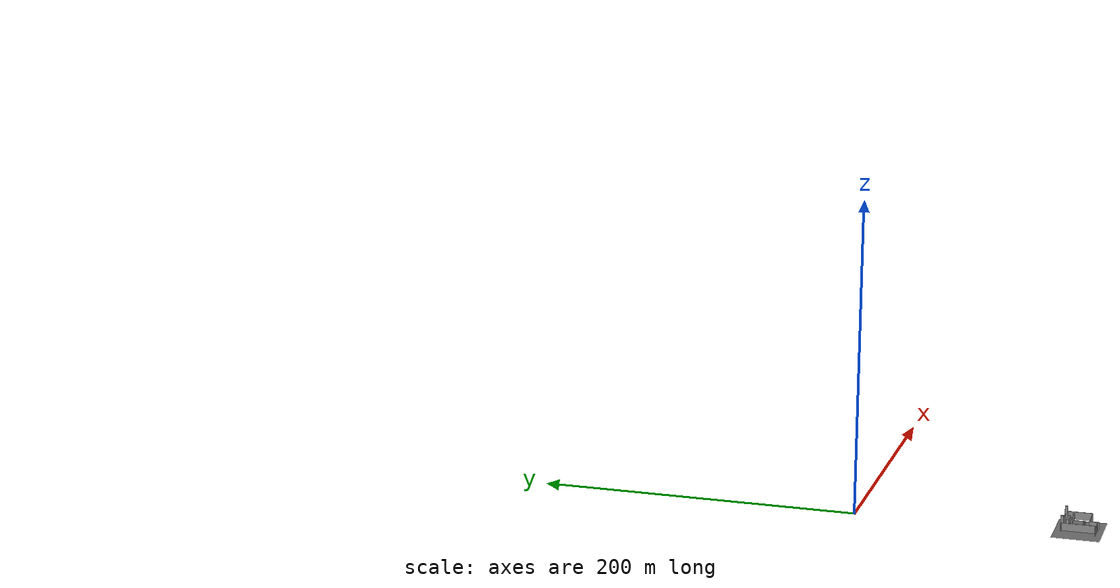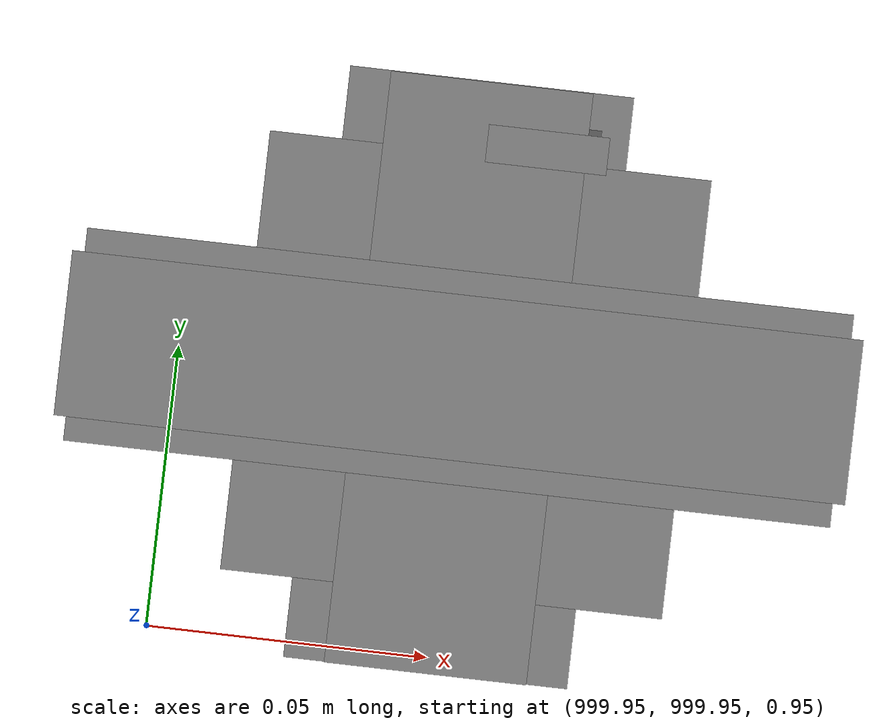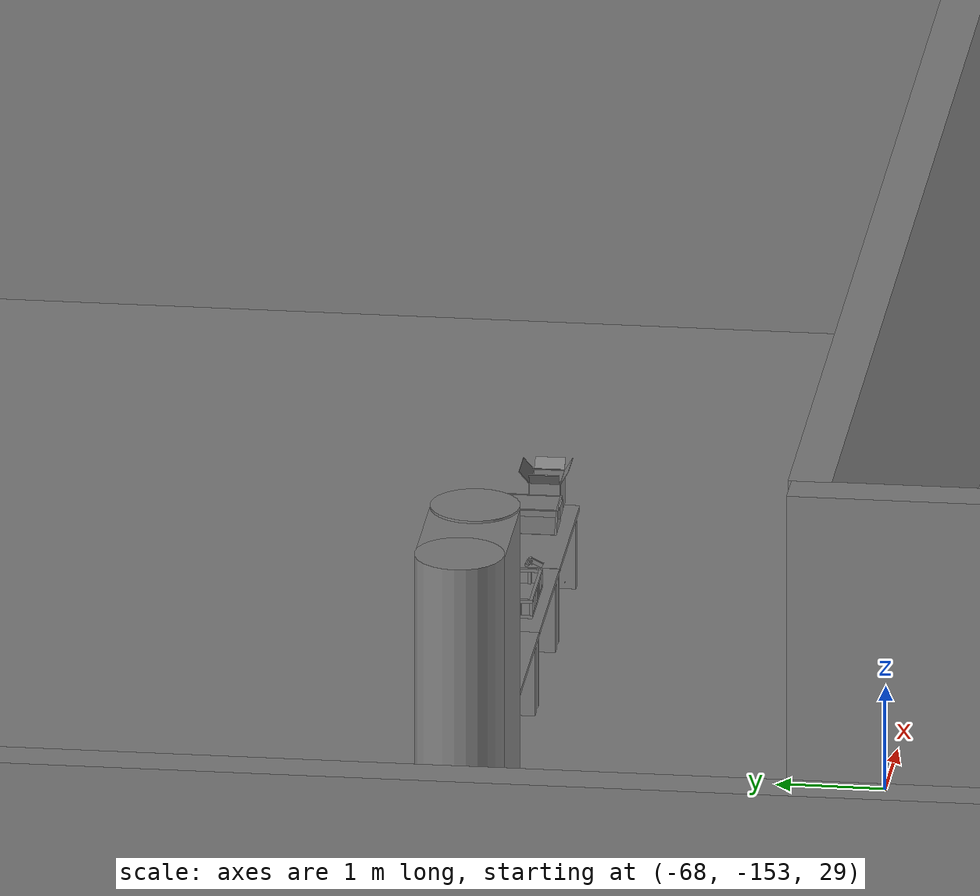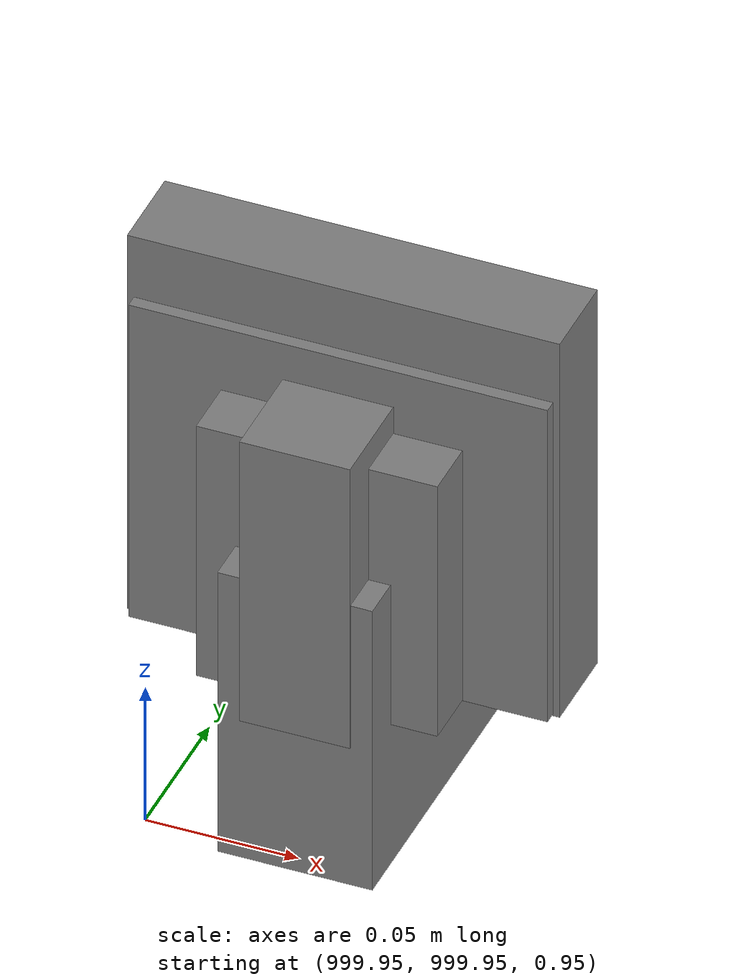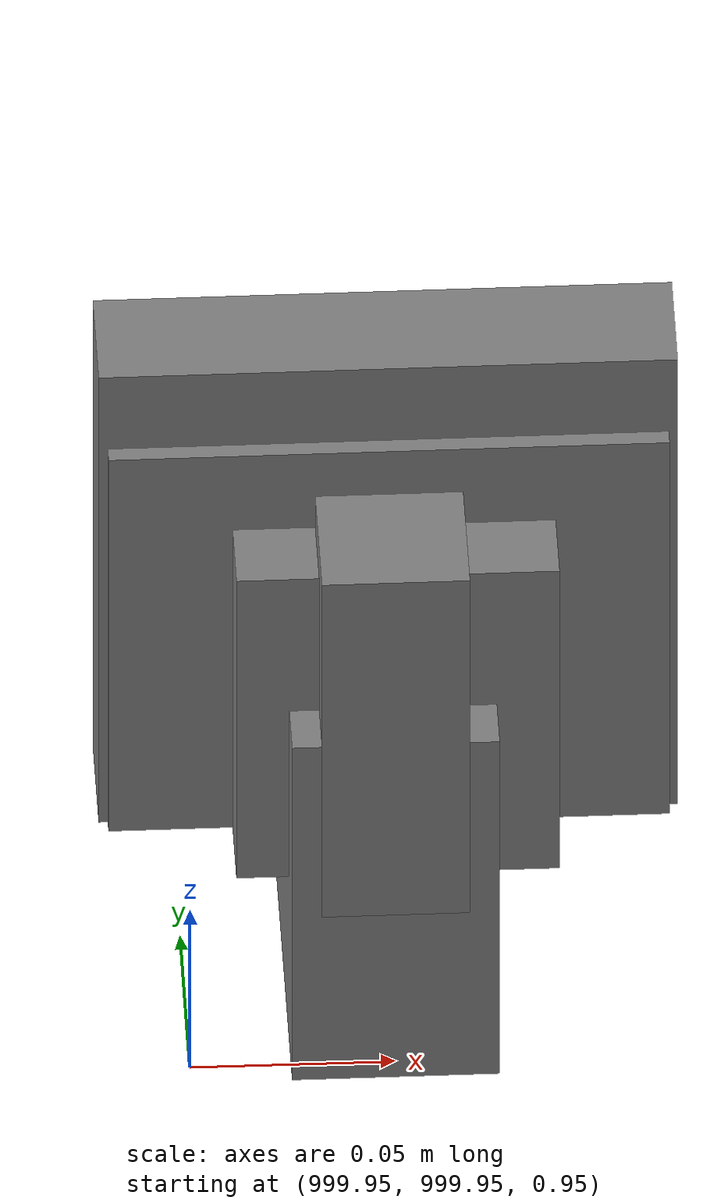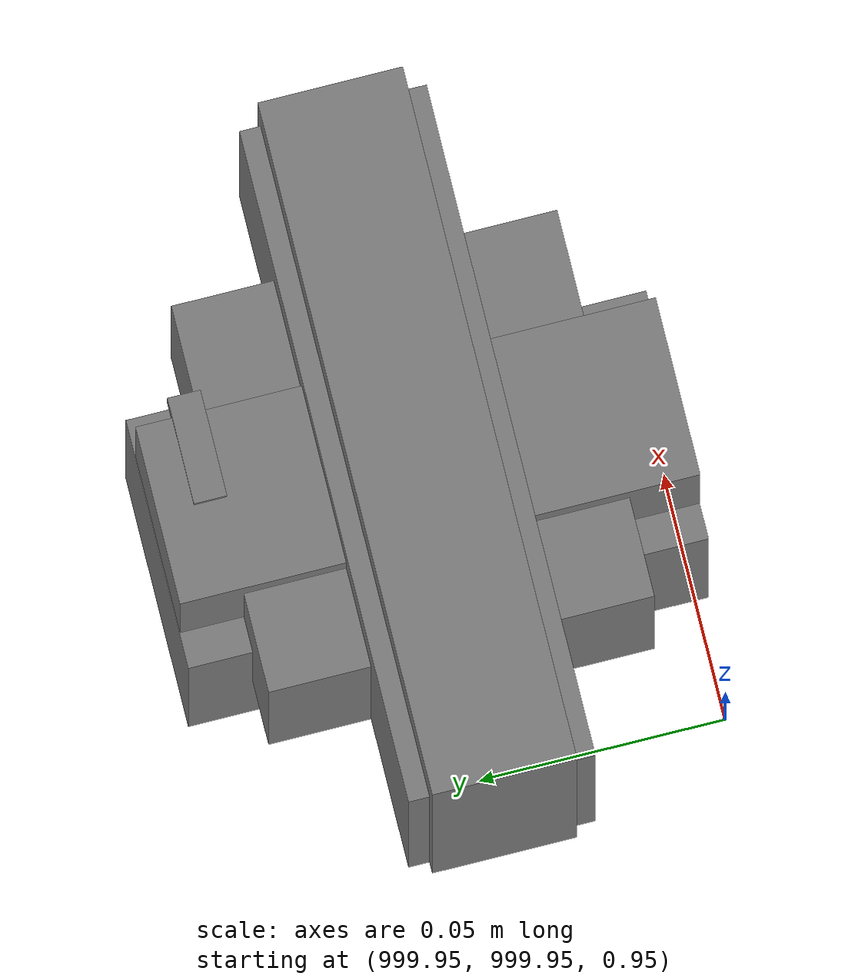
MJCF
<mujoco>
    <option gravity="0.000000000 0.000000000 -9.810000420" timestep="0.0049999999" integrator="implicitfast" density="1.225" viscosity="1.8000001e-05" noslip_iterations="10" iterations="100" sdf_iterations="50">
        <flag multiccd="disable"/>
    </option>
    <size memory="1000M"/>
    <compiler coordinate="local"/>
    <worldbody>
        <light cutoff="30" pos="0 1 1" dir="0 -1 -2"/>
        <light cutoff="30" pos="0 -1 1" dir="0 1 -2"/>
        <body pos="-66.369773865 -148.952728271 31.162240982" euler="44.161079407 43.801059723 -44.662227631" mocap="true" name="spotlight4_SpotLight"/>
        <body pos="1000.000000000 1000.000000000 1.000000000" euler="0.000000000 0.000000000 180.000000000" name="openloong_gripper_2f85_fix_base_usda_battery_01">
            <geom contype="1" conaffinity="1" density="1000" type="box" material="" rgba="0.500000000 0.500000000 0.500000000 1.000000000" solimp="0.899999976 0.949999988 0.001000000" friction="1.000000000 0.005000000 0.000100000" solref="0.020000000 1.000000000" margin="0" condim="3" group="0" pos="-0.011123657 -0.041940309 0.101691343" quat="1.000000000 0.000000000 0.000000000 0.000000000" size="0.010800000 0.003375000 0.004725000" name="openloong_gripper_2f85_fix_base_usda_geom_B777E60B_374A_416F_A425_9DCD68C5C517"/>
            <geom contype="1" conaffinity="1" density="1000" type="box" material="" rgba="0.500000000 0.500000000 0.500000000 1.000000000" solimp="0.899999976 0.949999988 0.001000000" friction="1.000000000 0.005000000 0.000100000" solref="0.020000000 1.000000000" margin="0" condim="3" group="0" pos="-0.010876465 -0.044247437 0.047066893" quat="0.998702705 -0.050920475 0.000000000 0.000000000" size="0.009450001 0.002700000 0.024975000" name="openloong_gripper_2f85_fix_base_usda_geom_6A337838_7674_444F_88D8_E00F6377E699"/>
            <geom contype="1" conaffinity="1" density="1000" type="box" material="" rgba="0.500000000 0.500000000 0.500000000 1.000000000" solimp="0.899999976 0.949999988 0.001000000" friction="1.000000000 0.005000000 0.000100000" solref="0.020000000 1.000000000" margin="0" condim="3" group="0" pos="-0.001235962 -0.000659180 0.047381196" quat="1.000000000 0.000000000 0.000000000 0.000000000" size="0.039420001 0.039150000 0.047250003" name="openloong_gripper_2f85_fix_base_usda_geom_FA082DB5_72A9_4886_8850_482605400047"/>
            <geom contype="1" conaffinity="1" density="1000" type="box" material="" rgba="0.500000000 0.500000000 0.500000000 1.000000000" solimp="0.899999976 0.949999988 0.001000000" friction="1.000000000 0.005000000 0.000100000" solref="0.020000000 1.000000000" margin="0" condim="3" group="0" pos="-0.010876465 -0.039138794 0.009851727" quat="1.000000000 0.000000000 0.000000000 0.000000000" size="0.009450001 0.010800000 0.013500000" name="openloong_gripper_2f85_fix_base_usda_geom_E4F57042_E267_4A76_9394_1CFDC41FB017"/>
            <geom contype="1" conaffinity="1" density="1000" type="box" material="" rgba="0.500000000 0.500000000 0.500000000 1.000000000" solimp="0.899999976 0.949999988 0.001000000" friction="1.000000000 0.005000000 0.000100000" solref="0.020000000 1.000000000" margin="0" condim="3" group="0" pos="-0.010876465 -0.041528322 0.071508206" quat="1.000000000 0.000000000 0.000000000 0.000000000" size="0.009450001 0.002700000 0.027000001" name="openloong_gripper_2f85_fix_base_usda_geom_E78ED04B_C6C9_404F_B2D0_08C1491A12D8"/>
            <freejoint name="openloong_gripper_2f85_fix_base_usda_battery_01_joint"/>
            <site size="0.005000000 0.005000000 0.005000000" rgba="0.500000000 0.500000000 0.500000000 1.000000000" pos="0.000000000 0.000000000 0.000000000" quat="0.999961913 0.008726500 0.000000000 0.000000000" group="0" type="sphere" name="openloong_gripper_2f85_fix_base_usda_battery_01site"/>
        </body>
        <body pos="1000.000000000 1000.000000000 1.000000000" euler="0.000000000 0.000000000 180.000000000" name="openloong_gripper_2f85_fix_base_usda_cpu_fan">
            <geom contype="1" conaffinity="1" density="1000" type="box" material="" rgba="0.500000000 0.500000000 0.500000000 1.000000000" solimp="0.899999976 0.949999988 0.001000000" friction="1.000000000 0.005000000 0.000100000" solref="0.020000000 1.000000000" margin="0" condim="3" group="0" pos="0.000000000 0.000000000 0.070034981" quat="0.000000000 0.000000000 0.000000000 1.000000000" size="0.070700005 0.014699999 0.070700005" name="openloong_gripper_2f85_fix_base_usda_geom_BC81059C_1473_4241_A68C_E55A29A8C2EA"/>
            <freejoint name="openloong_gripper_2f85_fix_base_usda_cpu_fan_joint"/>
            <site size="0.005000000 0.005000000 0.005000000" rgba="0.500000000 0.500000000 0.500000000 1.000000000" pos="0.000000000 0.000000000 0.000000000" quat="0.999961913 0.008726535 0.000000000 0.000000000" group="0" type="sphere" name="openloong_gripper_2f85_fix_base_usda_cpu_fancsite"/>
        </body>
        <body pos="1000.000000000 1000.000000000 1.000000000" euler="0.000000000 0.000000000 180.000000000" name="openloong_gripper_2f85_fix_base_usda_wifi_box">
            <geom contype="1" conaffinity="1" density="1000" type="box" material="" rgba="0.500000000 0.500000000 0.500000000 1.000000000" solimp="0.899999976 0.949999988 0.001000000" friction="1.000000000 0.005000000 0.000100000" solref="0.020000000 1.000000000" margin="0" condim="3" group="0" pos="0.000000000 0.000000000 0.058978677" quat="0.000000000 0.000000047 0.000000000 1.000000000" size="0.068499997 0.018999999 0.059000000" name="openloong_gripper_2f85_fix_base_usda_geom_2589211F_F23C_43FC_BC0C_70EAC5F41A76"/>
            <freejoint name="openloong_gripper_2f85_fix_base_usda_wifi_box_joint"/>
            <site size="0.005000000 0.005000000 0.005000000" rgba="0.500000000 0.500000000 0.500000000 1.000000000" pos="0.000000000 0.000000000 0.000000000" quat="0.999961913 0.008726500 0.000000000 0.000000000" group="0" type="sphere" name="openloong_gripper_2f85_fix_base_usda_wifi_boxsite"/>
        </body>
        <body pos="-65.921524048 -149.012100220 31.164577484" euler="-131.859344482 70.753982544 86.957893372" mocap="true" name="spotlight6_SpotLight"/>
        <body pos="1000.000000000 1000.000000000 1.000000000" euler="0.000011953 0.000005123 -179.999984741" name="openloong_gripper_2f85_fix_base_usda_intel_box">
            <geom contype="1" conaffinity="1" density="1000" type="box" material="" rgba="0.500000000 0.500000000 0.500000000 1.000000000" solimp="0.899999976 0.949999988 0.001000000" friction="1.000000000 0.005000000 0.000100000" solref="0.020000000 1.000000000" margin="0" condim="3" group="0" pos="0.000000000 -0.000067139 0.000082284" quat="0.707106709 0.000000225 0.000000253 0.707106650" size="0.052800003 0.025300000 0.052800003" name="openloong_gripper_2f85_fix_base_usda_geom_D2D8F30A_1ED1_4D0F_8AFF_20B4B666C5B0"/>
            <freejoint name="openloong_gripper_2f85_fix_base_usda_intel_box_joint"/>
            <site size="0.005000000 0.005000000 0.005000000" rgba="0.500000000 0.500000000 0.500000000 1.000000000" pos="0.000000000 0.000000000 0.000000000" quat="0.999961913 0.008726500 0.000000000 0.000000000" group="0" type="sphere" name="openloong_gripper_2f85_fix_base_usda_intel_boxsite"/>
        </body>
        <body pos="1000.000000000 999.999938965 1.000000000" euler="0.000000000 0.000000000 180.000000000" name="openloong_gripper_2f85_fix_base_usda_intelcore_i5">
            <geom contype="1" conaffinity="1" density="1000" type="box" material="" rgba="0.500000000 0.500000000 0.500000000 1.000000000" solimp="0.899999976 0.949999988 0.001000000" friction="1.000000000 0.005000000 0.000100000" solref="0.020000000 1.000000000" margin="0" condim="3" group="0" pos="0.000000000 0.000000000 0.051722717" quat="0.707106709 0.000000000 0.000000000 -0.707106769" size="0.052800000 0.018080002 0.052800000" name="openloong_gripper_2f85_fix_base_usda_geom_AA290259_2954_4B70_81FB_459430C5990D"/>
            <freejoint name="openloong_gripper_2f85_fix_base_usda_intelcore_i5_joint"/>
            <site size="0.005000000 0.005000000 0.005000000" rgba="0.500000000 0.500000000 0.500000000 1.000000000" pos="0.000000000 0.000000000 0.000000000" quat="0.999961913 0.008726534 0.000000000 0.000000000" group="0" type="sphere" name="openloong_gripper_2f85_fix_base_usda_intelcore_i5site"/>
        </body>
        <body pos="-66.215332031 -149.226776123 31.166009903" euler="-115.168296814 -81.329124451 73.322441101" mocap="true" name="spotlight2_SpotLight"/>
        <body pos="-64.866622925 -149.383972168 30.183746338" euler="89.999984741 89.999946594 0.000000000" name="openloong_gripper_2f85_fix_base_usda_bluebox_01">
            <geom contype="1" conaffinity="1" density="1000" type="box" material="" rgba="0.500000000 0.500000000 0.500000000 1.000000000" solimp="0.899999976 0.949999988 0.001000000" friction="1.000000000 0.005000000 0.000100000" solref="0.020000000 1.000000000" margin="0" condim="3" group="0" pos="0.276580811 0.187225342 0.000068665" quat="0.707106948 0.000077471 0.707106352 0.000077486" size="0.100000001 0.057999998 0.010000000" name="openloong_gripper_2f85_fix_base_usda_geom_0FB9264B_4346_4425_81C9_BDE3E31F31E0"/>
            <geom contype="1" conaffinity="1" density="1000" type="box" material="" rgba="0.500000000 0.500000000 0.500000000 1.000000000" solimp="0.899999976 0.949999988 0.001000000" friction="1.000000000 0.005000000 0.000100000" solref="0.020000000 1.000000000" margin="0" condim="3" group="0" pos="0.000000000 0.002883911 0.000000000" quat="0.999999881 0.000000000 0.000000000 0.000000000" size="0.254000008 0.003000000 0.172000006" name="openloong_gripper_2f85_fix_base_usda_geom_0F11DBF4_37A8_40B2_9BC4_15B7EC439561"/>
            <geom contype="1" conaffinity="1" density="1000" type="box" material="" rgba="0.500000000 0.500000000 0.500000000 1.000000000" solimp="0.899999976 0.949999988 0.001000000" friction="1.000000000 0.005000000 0.000100000" solref="0.020000000 1.000000000" margin="0" condim="3" group="0" pos="0.000000000 0.124874115 0.173484802" quat="0.999796331 0.020176515 -0.000000015 0.000000030" size="0.259999990 0.119999997 0.007000000" name="openloong_gripper_2f85_fix_base_usda_geom_886113F3_86D5_4039_82F3_594D60E14839"/>
            <geom contype="1" conaffinity="1" density="1000" type="box" material="" rgba="0.500000000 0.500000000 0.500000000 1.000000000" solimp="0.899999976 0.949999988 0.001000000" friction="1.000000000 0.005000000 0.000100000" solref="0.020000000 1.000000000" margin="0" condim="3" group="0" pos="0.000000000 0.124874115 -0.173469543" quat="0.999796331 -0.020176545 -0.000000015 0.000000000" size="0.259999990 0.119999997 0.007000000" name="openloong_gripper_2f85_fix_base_usda_geom_E9AF3E9C_FC4D_4202_84F4_32BA3E793423"/>
            <geom contype="1" conaffinity="1" density="1000" type="box" material="" rgba="0.500000000 0.500000000 0.500000000 1.000000000" solimp="0.899999976 0.949999988 0.001000000" friction="1.000000000 0.005000000 0.000100000" solref="0.020000000 1.000000000" margin="0" condim="3" group="0" pos="0.000000000 0.214008331 0.188980103" quat="0.999912977 0.013176724 0.000000015 0.000000000" size="0.259999990 0.029999999 0.012500000" name="openloong_gripper_2f85_fix_base_usda_geom_AB8CDEE2_74E4_4D24_B424_2267985A9691"/>
            <geom contype="1" conaffinity="1" density="1000" type="box" material="" rgba="0.500000000 0.500000000 0.500000000 1.000000000" solimp="0.899999976 0.949999988 0.001000000" friction="1.000000000 0.005000000 0.000100000" solref="0.020000000 1.000000000" margin="0" condim="3" group="0" pos="-0.258361816 0.125289917 0.001876831" quat="0.702796936 -0.020792112 0.710783124 0.020769298" size="0.189999998 0.119999997 0.009000000" name="openloong_gripper_2f85_fix_base_usda_geom_251594B3_F226_48DC_80D6_ED6C9BD520E8"/>
            <geom contype="1" conaffinity="1" density="1000" type="box" material="" rgba="0.500000000 0.500000000 0.500000000 1.000000000" solimp="0.899999976 0.949999988 0.001000000" friction="1.000000000 0.005000000 0.000100000" solref="0.020000000 1.000000000" margin="0" condim="3" group="0" pos="0.000000000 0.214008331 -0.188980103" quat="0.999912977 -0.013176769 0.000000030 0.000000015" size="0.259999990 0.029999999 0.012500000" name="openloong_gripper_2f85_fix_base_usda_geom_00B0897F_D5D6_43CB_A33D_AC3754E08EAE"/>
            <geom contype="1" conaffinity="1" density="1000" type="box" material="" rgba="0.500000000 0.500000000 0.500000000 1.000000000" solimp="0.899999976 0.949999988 0.001000000" friction="1.000000000 0.005000000 0.000100000" solref="0.020000000 1.000000000" margin="0" condim="3" group="0" pos="-0.276611328 0.187225342 0.000068665" quat="0.707106650 0.000077441 0.707106709 0.000077456" size="0.100000001 0.057999998 0.010000000" name="openloong_gripper_2f85_fix_base_usda_geom_A48A8ED0_4787_4E91_A690_D1D1C3241041"/>
            <geom contype="1" conaffinity="1" density="1000" type="box" material="" rgba="0.500000000 0.500000000 0.500000000 1.000000000" solimp="0.899999976 0.949999988 0.001000000" friction="1.000000000 0.005000000 0.000100000" solref="0.020000000 1.000000000" margin="0" condim="3" group="0" pos="0.258331299 0.125289917 0.001876831" quat="0.702851415 0.018856421 0.710823774 -0.019329369" size="0.189999998 0.119999997 0.009000000" name="openloong_gripper_2f85_fix_base_usda_geom_68A5F0E7_B457_45C5_B459_C962A2250CD2"/>
            <freejoint name="openloong_gripper_2f85_fix_base_usda_bluebox_01_joint"/>
            <site size="0.005000000 0.005000000 0.005000000" rgba="0.500000000 0.500000000 0.500000000 1.000000000" pos="0.000000000 0.000000000 0.000000000" quat="0.999961913 0.008726534 0.000000000 0.000000000" group="0" type="sphere" name="openloong_gripper_2f85_fix_base_usda_bluebox_01site"/>
        </body>
        <body pos="-64.496299744 -149.491867065 30.235729218" euler="0.000000000 0.000000000 89.999946594" name="openloong_gripper_2f85_fix_base_usda_cardboardbox_01">
            <geom contype="1" conaffinity="1" density="1000" type="box" material="" rgba="0.500000000 0.500000000 0.500000000 1.000000000" solimp="0.899999976 0.949999988 0.001000000" friction="1.000000000 0.005000000 0.000100000" solref="0.020000000 1.000000000" margin="0" condim="3" group="0" pos="-0.003166199 -0.004086494 0.005052090" quat="1.000000000 0.000000000 0.000000000 0.000000000" size="0.142499998 0.177500010 0.005000000" name="openloong_gripper_2f85_fix_base_usda_geom_33B08AFE_919F_4E98_BDFB_1049840E8958"/>
            <geom contype="1" conaffinity="1" density="1000" type="box" material="" rgba="0.500000000 0.500000000 0.500000000 1.000000000" solimp="0.899999976 0.949999988 0.001000000" friction="1.000000000 0.005000000 0.000100000" solref="0.020000000 1.000000000" margin="0" condim="3" group="0" pos="-0.003166199 0.170316696 0.150570869" quat="1.000000000 0.000000000 0.000000000 0.000000000" size="0.142499998 0.005000000 0.149999991" name="openloong_gripper_2f85_fix_base_usda_geom_CEE3EAFA_E2B7_4F42_B38C_9C6B3C34A669"/>
            <geom contype="1" conaffinity="1" density="1000" type="box" material="" rgba="0.500000000 0.500000000 0.500000000 1.000000000" solimp="0.899999976 0.949999988 0.001000000" friction="1.000000000 0.005000000 0.000100000" solref="0.020000000 1.000000000" margin="0" condim="3" group="0" pos="-0.147399902 -0.005307198 0.150570869" quat="1.000000000 0.000000000 0.000000000 0.000000000" size="0.005000000 0.177500010 0.149999991" name="openloong_gripper_2f85_fix_base_usda_geom_54A62843_8DEB_4B0D_ADC2_DACF13AA37CA"/>
            <geom contype="1" conaffinity="1" density="1000" type="box" material="" rgba="0.500000000 0.500000000 0.500000000 1.000000000" solimp="0.899999976 0.949999988 0.001000000" friction="1.000000000 0.005000000 0.000100000" solref="0.020000000 1.000000000" margin="0" condim="3" group="0" pos="0.140275955 -0.005307198 0.150570869" quat="1.000000000 0.000000000 0.000000000 0.000000000" size="0.005000000 0.177500010 0.149999991" name="openloong_gripper_2f85_fix_base_usda_geom_B2BFE5D9_210A_4C54_B6F1_6CFE94B5881A"/>
            <geom contype="1" conaffinity="1" density="1000" type="box" material="" rgba="0.500000000 0.500000000 0.500000000 1.000000000" solimp="0.899999976 0.949999988 0.001000000" friction="1.000000000 0.005000000 0.000100000" solref="0.020000000 1.000000000" margin="0" condim="3" group="0" pos="-0.003166199 -0.181550980 0.150570869" quat="1.000000000 0.000000000 0.000000000 0.000000000" size="0.142499998 0.005000000 0.149999991" name="openloong_gripper_2f85_fix_base_usda_geom_B8F7DA31_93B2_4BFB_918F_A2003666459D"/>
            <freejoint name="openloong_gripper_2f85_fix_base_usda_cardboardbox_01_joint"/>
            <site size="0.005000000 0.005000000 0.005000000" rgba="0.500000000 0.500000000 0.500000000 1.000000000" pos="0.000000000 0.000000000 0.000000000" quat="0.999961913 0.008726535 0.000000000 0.000000000" group="0" type="sphere" name="openloong_gripper_2f85_fix_base_usda_site_9AD227DC_5417_40F5_AD60_0FC48CC69D0B"/>
            <body pos="0.139160156 -0.004048347 0.301930904" euler="-179.999954224 49.383502960 179.999954224" name="openloong_gripper_2f85_fix_base_usda_A1_006">
                <geom contype="1" conaffinity="1" density="1000" type="box" material="" rgba="0.500000000 0.500000000 0.500000000 1.000000000" solimp="0.899999976 0.949999988 0.001000000" friction="1.000000000 0.005000000 0.000100000" solref="0.020000000 1.000000000" margin="0" condim="3" group="0" pos="-0.071587563 0.000009537 0.001745224" quat="0.999999881 0.000000000 0.000000000 0.000000000" size="0.071249999 0.179999992 0.002500000" name="openloong_gripper_2f85_fix_base_usda_geom_E7A95990_145F_4173_A4B7_2178E1287DE7"/>
                <joint armature="0" stiffness="0.07" damping="0.0099999998" axis="0.000000 1.000000 0.000000" type="hinge" name="openloong_gripper_2f85_fix_base_usda_A1_006"/>
            </body>
            <body pos="-0.145902634 -0.004086494 0.301938057" euler="-180.000000000 -60.000011444 -180.000000000" name="openloong_gripper_2f85_fix_base_usda_A2_006">
                <geom contype="1" conaffinity="1" density="1000" type="box" material="" rgba="0.500000000 0.500000000 0.500000000 1.000000000" solimp="0.899999976 0.949999988 0.001000000" friction="1.000000000 0.005000000 0.000100000" solref="0.020000000 1.000000000" margin="0" condim="3" group="0" pos="0.071268082 0.000009537 0.002717972" quat="0.000002921 0.000000000 -0.000000030 0.999999881" size="0.071249999 0.179999992 0.002500000" name="openloong_gripper_2f85_fix_base_usda_geom_AA6EF5FE_9E0A_4CAC_B0C9_C0EB4CA659D9"/>
                <joint armature="0" stiffness="0.07" damping="0.0099999998" axis="0.000000 1.000000 0.000000" type="hinge" name="openloong_gripper_2f85_fix_base_usda_A2_006"/>
            </body>
            <body pos="-0.003385544 0.175991058 0.301930904" euler="-125.858116150 -0.000004561 0.000002331" name="openloong_gripper_2f85_fix_base_usda_B2_006">
                <geom contype="1" conaffinity="1" density="1000" type="box" material="" rgba="0.500000000 0.500000000 0.500000000 1.000000000" solimp="0.899999976 0.949999988 0.001000000" friction="1.000000000 0.005000000 0.000100000" solref="0.020000000 1.000000000" margin="0" condim="3" group="0" pos="0.000009537 -0.070939064 -0.002470016" quat="0.999614120 0.027776197 -0.000000015 0.000000030" size="0.137500003 0.064999998 0.005000000" name="openloong_gripper_2f85_fix_base_usda_geom_190B553B_3788_4947_A036_11BA1542C19C"/>
                <joint armature="0" stiffness="0.07" damping="0.0099999998" axis="1.000000 0.000000 0.000000" type="hinge" name="openloong_gripper_2f85_fix_base_usda_B2_006"/>
            </body>
            <body pos="-0.003385544 -0.184140205 0.301938057" euler="147.805557251 0.000000000 0.000000000" name="openloong_gripper_2f85_fix_base_usda_B1_006">
                <geom contype="1" conaffinity="1" density="1000" type="box" material="" rgba="0.500000000 0.500000000 0.500000000 1.000000000" solimp="0.899999976 0.949999988 0.001000000" friction="1.000000000 0.005000000 0.000100000" solref="0.020000000 1.000000000" margin="0" condim="3" group="0" pos="-0.000028610 0.070202351 -0.002703667" quat="0.999614179 -0.027776167 0.000000000 0.000000000" size="0.137500003 0.064999998 0.005000000" name="openloong_gripper_2f85_fix_base_usda_geom_1ED4F010_F6A2_4938_8557_B89252C05382"/>
                <joint armature="0" stiffness="0.07" damping="0.0099999998" axis="1.000000 0.000000 0.000000" type="hinge" name="openloong_gripper_2f85_fix_base_usda_B1_006"/>
            </body>
        </body>
        <body pos="-65.882858276 -149.481979370 30.229999542" euler="-64.487716675 0.000000000 0.000000000" name="openloong_gripper_2f85_fix_base_usda_Barcode">
            <geom contype="1" conaffinity="1" density="1000" type="box" material="" rgba="0.500000000 0.500000000 0.500000000 1.000000000" solimp="0.899999976 0.949999988 0.001000000" friction="1.000000000 0.005000000 0.000100000" solref="0.020000000 1.000000000" margin="0" condim="3" group="0" pos="0.000000000 0.013038635 0.001419067" quat="0.000000000 0.000000000 0.000000000 1.000000119" size="0.034000002 0.010000000 0.017999999" name="openloong_gripper_2f85_fix_base_usda_geom_98CE266E_B7A5_4AB7_AAF6_4AC7DA12E58B"/>
            <geom contype="1" conaffinity="1" density="1000" type="box" material="" rgba="0.500000000 0.500000000 0.500000000 1.000000000" solimp="0.899999976 0.949999988 0.001000000" friction="1.000000000 0.005000000 0.000100000" solref="0.020000000 1.000000000" margin="0" condim="3" group="0" pos="0.000000000 -0.035301208 -0.007095337" quat="0.000000000 0.000000000 -0.043619365 0.999048233" size="0.028999999 0.010000000 0.020000000" name="openloong_gripper_2f85_fix_base_usda_geom_C61E25C8_EF54_4EE9_8F33_66339632CD3C"/>
            <geom contype="1" conaffinity="1" density="1000" type="box" material="" rgba="0.500000000 0.500000000 0.500000000 1.000000000" solimp="0.899999976 0.949999988 0.001000000" friction="1.000000000 0.005000000 0.000100000" solref="0.020000000 1.000000000" margin="0" condim="3" group="0" pos="0.000000000 -0.043411255 -0.011749268" quat="0.922262907 0.386563420 0.000000000 0.000000000" size="0.026000001 0.010000000 0.020000000" name="openloong_gripper_2f85_fix_base_usda_geom_676DAD16_B1EA_4F70_BCAF_69F97B402A71"/>
            <geom contype="1" conaffinity="1" density="1000" type="box" material="" rgba="0.500000000 0.500000000 0.500000000 1.000000000" solimp="0.899999976 0.949999988 0.001000000" friction="1.000000000 0.005000000 0.000100000" solref="0.020000000 1.000000000" margin="0" condim="3" group="0" pos="0.000000000 -0.016967773 -0.031860352" quat="0.000000000 0.000000000 0.000000000 1.000000119" size="0.008000000 0.010000000 0.013000000" name="openloong_gripper_2f85_fix_base_usda_geom_DA0EE49B_F013_4C54_B72D_C3ED990089F5"/>
            <geom contype="1" conaffinity="1" density="1000" type="box" material="" rgba="0.500000000 0.500000000 0.500000000 1.000000000" solimp="0.899999976 0.949999988 0.001000000" friction="1.000000000 0.005000000 0.000100000" solref="0.020000000 1.000000000" margin="0" condim="3" group="0" pos="0.000000000 -0.001869202 0.000312805" quat="0.953716993 0.300705761 0.000000000 0.000000000" size="0.032000002 0.010000000 0.018999999" name="openloong_gripper_2f85_fix_base_usda_geom_85AF6D3B_F7A4_490A_8083_288D487AFBC4"/>
            <geom contype="1" conaffinity="1" density="1000" type="box" material="" rgba="0.500000000 0.500000000 0.500000000 1.000000000" solimp="0.899999976 0.949999988 0.001000000" friction="1.000000000 0.005000000 0.000100000" solref="0.020000000 1.000000000" margin="0" condim="3" group="0" pos="0.000000000 -0.019531250 -0.003173828" quat="0.953716993 0.300705761 0.000000000 0.000000000" size="0.030999999 0.010000000 0.020000000" name="openloong_gripper_2f85_fix_base_usda_geom_CC6FF6A4_A629_4FDF_8246_4834C7B3A9DA"/>
            <geom contype="1" conaffinity="1" density="1000" type="box" material="" rgba="0.500000000 0.500000000 0.500000000 1.000000000" solimp="0.899999976 0.949999988 0.001000000" friction="1.000000000 0.005000000 0.000100000" solref="0.020000000 1.000000000" margin="0" condim="3" group="0" pos="0.000000000 -0.035301208 -0.007095337" quat="0.953716993 0.300705761 0.000000000 0.000000000" size="0.028999999 0.010000000 0.020000000" name="openloong_gripper_2f85_fix_base_usda_geom_6CC92107_DCEF_418B_8D99_6F228772E89C"/>
            <geom contype="1" conaffinity="1" density="1000" type="box" material="" rgba="0.500000000 0.500000000 0.500000000 1.000000000" solimp="0.899999976 0.949999988 0.001000000" friction="1.000000000 0.005000000 0.000100000" solref="0.020000000 1.000000000" margin="0" condim="3" group="0" pos="0.000000000 -0.042617798 -0.071121216" quat="0.000000000 0.000000000 0.000000000 1.000000119" size="0.013000000 0.021000000 0.059999999" name="openloong_gripper_2f85_fix_base_usda_geom_8D851AF1_2388_4CB8_A421_915B04BB347D"/>
            <freejoint name="openloong_gripper_2f85_fix_base_usda_Barcode_joint"/>
            <site size="0.005000000 0.005000000 0.005000000" rgba="0.500000000 0.500000000 0.500000000 1.000000000" pos="0.000000000 0.000000000 0.000000000" quat="1.000000000 0.000000000 0.000000000 0.000000000" group="0" type="sphere" name="openloong_gripper_2f85_fix_base_usda_Barcode_site"/>
        </body>
        <body pos="-66.745018005 -149.392349243 30.184000015" euler="0.000000000 0.000000000 89.999946594" name="[22333301318043]_Basket_01">
            <geom contype="1" conaffinity="1" density="1000" type="box" material="" rgba="0.500000000 0.500000000 0.500000000 1.000000000" solimp="0.899999976 0.949999988 0.001000000" friction="1.000000000 0.005000000 0.000100000" solref="0.020000000 1.000000000" margin="0" condim="3" group="0" pos="-0.052425385 0.389207840 0.089787483" quat="0.707107008 0.000000000 0.000000000 0.707106411" size="0.014249999 0.014249999 0.059999999" name="[22333301318043]_geom_656D9D5A_706B_4A37_B389_4B071F5743A8"/>
            <geom contype="1" conaffinity="1" density="1000" type="box" material="" rgba="0.500000000 0.500000000 0.500000000 1.000000000" solimp="0.899999976 0.949999988 0.001000000" friction="1.000000000 0.005000000 0.000100000" solref="0.020000000 1.000000000" margin="0" condim="3" group="0" pos="0.264015198 -0.133043289 0.089787483" quat="0.707107008 0.000000000 0.000000000 0.707106411" size="0.014249999 0.014249999 0.059999999" name="[22333301318043]_geom_F8E83B10_7504_443E_A696_EA0168DE8B98"/>
            <geom contype="1" conaffinity="1" density="1000" type="box" material="" rgba="0.500000000 0.500000000 0.500000000 1.000000000" solimp="0.899999976 0.949999988 0.001000000" friction="1.000000000 0.005000000 0.000100000" solref="0.020000000 1.000000000" margin="0" condim="3" group="0" pos="-0.264015198 -0.265548706 0.089793205" quat="0.707107008 0.000000000 0.000000000 0.707106411" size="0.014249999 0.014249999 0.059999999" name="[22333301318043]_geom_E0B6AF73_B163_40C8_98FB_40BF81FECB12"/>
            <geom contype="1" conaffinity="1" density="1000" type="box" material="" rgba="0.500000000 0.500000000 0.500000000 1.000000000" solimp="0.899999976 0.949999988 0.001000000" friction="1.000000000 0.005000000 0.000100000" solref="0.020000000 1.000000000" margin="0" condim="3" group="0" pos="-0.160263062 -0.389322281 0.089793205" quat="0.707107008 0.000000000 0.000000000 0.707106411" size="0.014249999 0.014249999 0.059999999" name="[22333301318043]_geom_447A9130_D508_4544_A502_5B716792856C"/>
            <geom contype="1" conaffinity="1" density="1000" type="box" material="" rgba="0.500000000 0.500000000 0.500000000 1.000000000" solimp="0.899999976 0.949999988 0.001000000" friction="1.000000000 0.005000000 0.000100000" solref="0.020000000 1.000000000" margin="0" condim="3" group="0" pos="0.162265778 -0.389322281 0.089787483" quat="0.707107008 0.000000000 0.000000000 0.707106411" size="0.014249999 0.014249999 0.059999999" name="[22333301318043]_geom_18538E86_F4B3_4A68_80A2_9E3EAC8548A9"/>
            <geom contype="1" conaffinity="1" density="1000" type="box" material="" rgba="0.500000000 0.500000000 0.500000000 1.000000000" solimp="0.899999976 0.949999988 0.001000000" friction="1.000000000 0.005000000 0.000100000" solref="0.020000000 1.000000000" margin="0" condim="3" group="0" pos="0.264015198 0.389207840 0.089787483" quat="0.707107008 0.000000000 0.000000000 0.707106411" size="0.014249999 0.014249999 0.059999999" name="[22333301318043]_geom_1241C617_53FF_49F8_ACC7_EDF015DDF253"/>
            <geom contype="1" conaffinity="1" density="1000" type="box" material="" rgba="0.500000000 0.500000000 0.500000000 1.000000000" solimp="0.899999976 0.949999988 0.001000000" friction="1.000000000 0.005000000 0.000100000" solref="0.020000000 1.000000000" margin="0" condim="3" group="0" pos="-0.264015198 -0.133043289 0.089793205" quat="0.707107008 0.000000000 0.000000000 0.707106411" size="0.014249999 0.014249999 0.059999999" name="[22333301318043]_geom_DED8F8F4_34CD_4FC4_B102_41042F256E0D"/>
            <geom contype="1" conaffinity="1" density="1000" type="box" material="" rgba="0.500000000 0.500000000 0.500000000 1.000000000" solimp="0.899999976 0.949999988 0.001000000" friction="1.000000000 0.005000000 0.000100000" solref="0.020000000 1.000000000" margin="0" condim="3" group="0" pos="-0.264026642 0.269256592 0.089793205" quat="0.707107008 0.000000000 0.000000000 0.707106411" size="0.014249999 0.014249999 0.059999999" name="[22333301318043]_geom_D0CCD5B3_4950_4E58_ACAD_5520F7383947"/>
            <geom contype="1" conaffinity="1" density="1000" type="box" material="" rgba="0.500000000 0.500000000 0.500000000 1.000000000" solimp="0.899999976 0.949999988 0.001000000" friction="1.000000000 0.005000000 0.000100000" solref="0.020000000 1.000000000" margin="0" condim="3" group="0" pos="0.054462433 0.389207840 0.089787483" quat="0.707107008 0.000000000 0.000000000 0.707106411" size="0.014249999 0.014249999 0.059999999" name="[22333301318043]_geom_F57BEA1F_8E82_42EF_8841_E96443EC42CF"/>
            <geom contype="1" conaffinity="1" density="1000" type="box" material="" rgba="0.500000000 0.500000000 0.500000000 1.000000000" solimp="0.899999976 0.949999988 0.001000000" friction="1.000000000 0.005000000 0.000100000" solref="0.020000000 1.000000000" margin="0" condim="3" group="0" pos="0.054462433 -0.389322281 0.089787483" quat="0.707107008 0.000000000 0.000000000 0.707106411" size="0.014249999 0.014249999 0.059999999" name="[22333301318043]_geom_F6F587A9_A59A_474A_B485_834994A19FBB"/>
            <geom contype="1" conaffinity="1" density="1000" type="box" material="" rgba="0.500000000 0.500000000 0.500000000 1.000000000" solimp="0.899999976 0.949999988 0.001000000" friction="1.000000000 0.005000000 0.000100000" solref="0.020000000 1.000000000" margin="0" condim="3" group="0" pos="0.264015198 0.269256592 0.089793205" quat="0.707107008 0.000000000 0.000000000 0.707106411" size="0.014249999 0.014249999 0.059999999" name="[22333301318043]_geom_B7337462_8C63_48AE_A502_466C565A6E72"/>
            <geom contype="1" conaffinity="1" density="1000" type="box" material="" rgba="0.500000000 0.500000000 0.500000000 1.000000000" solimp="0.899999976 0.949999988 0.001000000" friction="1.000000000 0.005000000 0.000100000" solref="0.020000000 1.000000000" margin="0" condim="3" group="0" pos="0.264015198 -0.389322281 0.089787483" quat="0.707107008 0.000000000 0.000000000 0.707106411" size="0.014249999 0.014249999 0.059999999" name="[22333301318043]_geom_9108F9B5_830A_4D2A_8DB0_757117EA52BB"/>
            <geom contype="1" conaffinity="1" density="1000" type="box" material="" rgba="0.500000000 0.500000000 0.500000000 1.000000000" solimp="0.899999976 0.949999988 0.001000000" friction="1.000000000 0.005000000 0.000100000" solref="0.020000000 1.000000000" margin="0" condim="3" group="0" pos="0.000000000 0.000000000 0.015998840" quat="0.707107008 0.000000000 0.000000000 0.707106411" size="0.403499991 0.279000014 0.015750000" name="[22333301318043]_geom_B2DBD5A4_4AB3_4D5B_B430_9F91D0501D61"/>
            <geom contype="1" conaffinity="1" density="1000" type="box" material="" rgba="0.500000000 0.500000000 0.500000000 1.000000000" solimp="0.899999976 0.949999988 0.001000000" friction="1.000000000 0.005000000 0.000100000" solref="0.020000000 1.000000000" margin="0" condim="3" group="0" pos="0.000000000 -0.389476776 0.163619041" quat="0.707107008 0.000000000 0.000000000 0.707106411" size="0.015000000 0.277500004 0.015750000" name="[22333301318043]_geom_169B8315_657B_4145_BF92_869B6C4C3AC6"/>
            <geom contype="1" conaffinity="1" density="1000" type="box" material="" rgba="0.500000000 0.500000000 0.500000000 1.000000000" solimp="0.899999976 0.949999988 0.001000000" friction="1.000000000 0.005000000 0.000100000" solref="0.020000000 1.000000000" margin="0" condim="3" group="0" pos="0.162265778 0.389207840 0.089787483" quat="0.707107008 0.000000000 0.000000000 0.707106411" size="0.014249999 0.014249999 0.059999999" name="[22333301318043]_geom_2F361F94_46FE_447B_9C2B_C2F1B238DB43"/>
            <geom contype="1" conaffinity="1" density="1000" type="box" material="" rgba="0.500000000 0.500000000 0.500000000 1.000000000" solimp="0.899999976 0.949999988 0.001000000" friction="1.000000000 0.005000000 0.000100000" solref="0.020000000 1.000000000" margin="0" condim="3" group="0" pos="0.000000000 0.389471054 0.163619041" quat="0.707107008 0.000000000 0.000000000 0.707106411" size="0.015000000 0.277500004 0.015750000" name="[22333301318043]_geom_56E4A7C5_63CC_4554_BF02_C78B487FE6E0"/>
            <geom contype="1" conaffinity="1" density="1000" type="box" material="" rgba="0.500000000 0.500000000 0.500000000 1.000000000" solimp="0.899999976 0.949999988 0.001000000" friction="1.000000000 0.005000000 0.000100000" solref="0.020000000 1.000000000" margin="0" condim="3" group="0" pos="-0.263511658 0.000000000 0.163619041" quat="0.707107008 0.000000000 0.000000000 0.707106411" size="0.403499991 0.015000000 0.015750000" name="[22333301318043]_geom_A326D512_BD26_40C8_82BA_D44298ABF578"/>
            <geom contype="1" conaffinity="1" density="1000" type="box" material="" rgba="0.500000000 0.500000000 0.500000000 1.000000000" solimp="0.899999976 0.949999988 0.001000000" friction="1.000000000 0.005000000 0.000100000" solref="0.020000000 1.000000000" margin="0" condim="3" group="0" pos="-0.264015198 0.141334534 0.089793205" quat="0.707107008 0.000000000 0.000000000 0.707106411" size="0.014249999 0.014249999 0.059999999" name="[22333301318043]_geom_163ECEEB_975B_47AE_9F1E_761ED9CD3C35"/>
            <geom contype="1" conaffinity="1" density="1000" type="box" material="" rgba="0.500000000 0.500000000 0.500000000 1.000000000" solimp="0.899999976 0.949999988 0.001000000" friction="1.000000000 0.005000000 0.000100000" solref="0.020000000 1.000000000" margin="0" condim="3" group="0" pos="0.264015198 -0.265548706 0.089787483" quat="0.707107008 0.000000000 0.000000000 0.707106411" size="0.014249999 0.014249999 0.059999999" name="[22333301318043]_geom_0538F8BA_7D42_472B_887B_2453D9F573F4"/>
            <geom contype="1" conaffinity="1" density="1000" type="box" material="" rgba="0.500000000 0.500000000 0.500000000 1.000000000" solimp="0.899999976 0.949999988 0.001000000" friction="1.000000000 0.005000000 0.000100000" solref="0.020000000 1.000000000" margin="0" condim="3" group="0" pos="-0.160263062 0.389207840 0.089787483" quat="0.707107008 0.000000000 0.000000000 0.707106411" size="0.014249999 0.014249999 0.059999999" name="[22333301318043]_geom_3E9AC9E8_D812_4B30_83A2_D71B0263B1AB"/>
            <geom contype="1" conaffinity="1" density="1000" type="box" material="" rgba="0.500000000 0.500000000 0.500000000 1.000000000" solimp="0.899999976 0.949999988 0.001000000" friction="1.000000000 0.005000000 0.000100000" solref="0.020000000 1.000000000" margin="0" condim="3" group="0" pos="-0.052425385 -0.389322281 0.089787483" quat="0.707107008 0.000000000 0.000000000 0.707106411" size="0.014249999 0.014249999 0.059999999" name="[22333301318043]_geom_1EFBBDE0_B7A2_4F51_A292_CECFE47A5FD8"/>
            <geom contype="1" conaffinity="1" density="1000" type="box" material="" rgba="0.500000000 0.500000000 0.500000000 1.000000000" solimp="0.899999976 0.949999988 0.001000000" friction="1.000000000 0.005000000 0.000100000" solref="0.020000000 1.000000000" margin="0" condim="3" group="0" pos="-0.264026642 -0.389322281 0.089793205" quat="0.707107008 0.000000000 0.000000000 0.707106411" size="0.014249999 0.014249999 0.059999999" name="[22333301318043]_geom_A93E6512_4BE6_4E05_AEBE_2790BCE6ECE9"/>
            <geom contype="1" conaffinity="1" density="1000" type="box" material="" rgba="0.500000000 0.500000000 0.500000000 1.000000000" solimp="0.899999976 0.949999988 0.001000000" friction="1.000000000 0.005000000 0.000100000" solref="0.020000000 1.000000000" margin="0" condim="3" group="0" pos="0.264015198 0.141334534 0.089787483" quat="0.707107008 0.000000000 0.000000000 0.707106411" size="0.014249999 0.014249999 0.059999999" name="[22333301318043]_geom_1A12B4A3_B750_45E1_981F_AAD23B8C6CAF"/>
            <geom contype="1" conaffinity="1" density="1000" type="box" material="" rgba="0.500000000 0.500000000 0.500000000 1.000000000" solimp="0.899999976 0.949999988 0.001000000" friction="1.000000000 0.005000000 0.000100000" solref="0.020000000 1.000000000" margin="0" condim="3" group="0" pos="-0.264015198 0.389207840 0.089793205" quat="0.707107008 0.000000000 0.000000000 0.707106411" size="0.014249999 0.014249999 0.059999999" name="[22333301318043]_geom_8FFB668E_705E_4FC7_B86A_AA0FEB9869ED"/>
            <geom contype="1" conaffinity="1" density="1000" type="box" material="" rgba="0.500000000 0.500000000 0.500000000 1.000000000" solimp="0.899999976 0.949999988 0.001000000" friction="1.000000000 0.005000000 0.000100000" solref="0.020000000 1.000000000" margin="0" condim="3" group="0" pos="0.264015198 0.004480362 0.089787483" quat="0.707107008 0.000000000 0.000000000 0.707106411" size="0.014249999 0.014249999 0.059999999" name="[22333301318043]_geom_7720DAB4_5604_45C9_96A9_1B306D450C43"/>
            <geom contype="1" conaffinity="1" density="1000" type="box" material="" rgba="0.500000000 0.500000000 0.500000000 1.000000000" solimp="0.899999976 0.949999988 0.001000000" friction="1.000000000 0.005000000 0.000100000" solref="0.020000000 1.000000000" margin="0" condim="3" group="0" pos="0.263694763 -0.000011444 0.163619041" quat="0.707107008 0.000000000 0.000000000 0.707106411" size="0.403499991 0.015000000 0.015750000" name="[22333301318043]_geom_665351D2_A69F_4954_9711_2E0BACE8DDCD"/>
            <geom contype="1" conaffinity="1" density="1000" type="box" material="" rgba="0.500000000 0.500000000 0.500000000 1.000000000" solimp="0.899999976 0.949999988 0.001000000" friction="1.000000000 0.005000000 0.000100000" solref="0.020000000 1.000000000" margin="0" condim="3" group="0" pos="-0.264015198 0.004480362 0.089793205" quat="0.707107008 0.000000000 0.000000000 0.707106411" size="0.014249999 0.014249999 0.059999999" name="[22333301318043]_geom_4A32B1BE_9535_4F76_8EF3_3C484068CFA0"/>
            <freejoint name="[22333301318043]_joint_29BB22DE_0B37_438E_8E76_82CB3938B09E"/>
        </body>
        <body pos="0.000000000 0.000000000 0.000000000" euler="0.000000000 0.000000000 0.000000000" name="Static Objects_Static Objects">
            <geom contype="1" conaffinity="1" density="1000" type="box" material="" rgba="0.500000000 0.500000000 0.500000000 1.000000000" solimp="0.899999976 0.949999988 0.001000000" friction="1.000000000 0.005000000 0.000100000" solref="0.020000000 1.000000000" margin="0" condim="3" group="0" pos="-67.544113159 -149.365814209 29.727830887" quat="0.500000417 0.499999970 0.499999553 0.499999970" size="0.381000012 0.319999993 0.041000001" name="Static Objects_geom_C3305AEE_74A5_4093_89B4_B3ADC9A8C057"/>
            <geom contype="1" conaffinity="1" density="1000" type="box" material="" rgba="0.500000000 0.500000000 0.500000000 1.000000000" solimp="0.899999976 0.949999988 0.001000000" friction="1.000000000 0.005000000 0.000100000" solref="0.020000000 1.000000000" margin="0" condim="3" group="0" pos="-68.239501953 -149.365814209 30.086868286" quat="0.500000417 0.499999970 0.499999553 0.499999970" size="0.370999992 0.039500002 0.745000005" name="Static Objects_geom_D7BE6837_8B96_4C6F_9525_4268C36D0B83"/>
            <geom contype="1" conaffinity="1" density="1000" type="box" material="" rgba="0.500000000 0.500000000 0.500000000 1.000000000" solimp="0.899999976 0.949999988 0.001000000" friction="1.000000000 0.005000000 0.000100000" solref="0.020000000 1.000000000" margin="0" condim="3" group="0" pos="-68.239501953 -149.365814209 30.147235870" quat="0.500000417 0.499999970 0.499999553 0.499999970" size="0.400000006 0.022000000 0.800000012" name="Static Objects_geom_2862A20A_A737_4C77_8D75_B5A8ED9C23BA"/>
            <geom contype="1" conaffinity="1" density="1000" type="box" material="" rgba="0.500000000 0.500000000 0.500000000 1.000000000" solimp="0.899999976 0.949999988 0.001000000" friction="1.000000000 0.005000000 0.000100000" solref="0.020000000 1.000000000" margin="0" condim="3" group="0" pos="-68.934890747 -149.365814209 29.727830887" quat="0.500000417 0.499999970 0.499999553 0.499999970" size="0.381000012 0.319999993 0.041000001" name="Static Objects_geom_C9F5A331_FB11_4CA3_91CA_49E2F33FBE02"/>
            <geom contype="1" conaffinity="1" density="1000" type="box" material="" rgba="0.500000000 0.500000000 0.500000000 1.000000000" solimp="0.899999976 0.949999988 0.001000000" friction="1.000000000 0.005000000 0.000100000" solref="0.020000000 1.000000000" margin="0" condim="3" group="0" pos="-68.239501953 -149.365814209 29.561563492" quat="0.500000417 0.499999970 0.499999553 0.499999970" size="0.020000000 0.022000000 0.660000026" name="Static Objects_geom_9EECD3C9_56E8_4F45_8C5C_CC33EA6D28CF"/>
            <geom contype="1" conaffinity="1" density="1000" type="box" material="" rgba="0.500000000 0.500000000 0.500000000 1.000000000" solimp="0.899999976 0.949999988 0.001000000" friction="1.000000000 0.005000000 0.000100000" solref="0.020000000 1.000000000" margin="0" condim="3" group="0" pos="-65.945671082 -149.365814209 29.727830887" quat="0.500000417 0.499999970 0.499999553 0.499999970" size="0.381000012 0.319999993 0.041000001" name="Static Objects_geom_3FB6F44A_1F15_4E7C_8383_476C4EAF265C"/>
            <geom contype="1" conaffinity="1" density="1000" type="box" material="" rgba="0.500000000 0.500000000 0.500000000 1.000000000" solimp="0.899999976 0.949999988 0.001000000" friction="1.000000000 0.005000000 0.000100000" solref="0.020000000 1.000000000" margin="0" condim="3" group="0" pos="-66.641059875 -149.365814209 30.086868286" quat="0.500000417 0.499999970 0.499999553 0.499999970" size="0.370999992 0.039500002 0.745000005" name="Static Objects_geom_CAE77309_EBE4_4D8D_AF70_8C018C8D921A"/>
            <geom contype="1" conaffinity="1" density="1000" type="box" material="" rgba="0.500000000 0.500000000 0.500000000 1.000000000" solimp="0.899999976 0.949999988 0.001000000" friction="1.000000000 0.005000000 0.000100000" solref="0.020000000 1.000000000" margin="0" condim="3" group="0" pos="-66.641059875 -149.365814209 30.147235870" quat="0.500000417 0.499999970 0.499999553 0.499999970" size="0.400000006 0.022000000 0.800000012" name="Static Objects_geom_85F72397_562B_479E_9F57_42F661874E41"/>
            <geom contype="1" conaffinity="1" density="1000" type="box" material="" rgba="0.500000000 0.500000000 0.500000000 1.000000000" solimp="0.899999976 0.949999988 0.001000000" friction="1.000000000 0.005000000 0.000100000" solref="0.020000000 1.000000000" margin="0" condim="3" group="0" pos="-67.336448669 -149.365814209 29.727830887" quat="0.500000417 0.499999970 0.499999553 0.499999970" size="0.381000012 0.319999993 0.041000001" name="Static Objects_geom_64557040_B77C_44F6_8BF4_E81A3BDED9DB"/>
            <geom contype="1" conaffinity="1" density="1000" type="box" material="" rgba="0.500000000 0.500000000 0.500000000 1.000000000" solimp="0.899999976 0.949999988 0.001000000" friction="1.000000000 0.005000000 0.000100000" solref="0.020000000 1.000000000" margin="0" condim="3" group="0" pos="-66.641059875 -149.365814209 29.561563492" quat="0.500000417 0.499999970 0.499999553 0.499999970" size="0.020000000 0.022000000 0.660000026" name="Static Objects_geom_673BC780_F4CB_4840_A261_6AAC29C9EC71"/>
            <geom contype="1" conaffinity="1" density="1000" type="box" material="" rgba="0.500000000 0.500000000 0.500000000 1.000000000" solimp="0.899999976 0.949999988 0.001000000" friction="1.000000000 0.005000000 0.000100000" solref="0.020000000 1.000000000" margin="0" condim="3" group="0" pos="-64.338577271 -149.365814209 29.727830887" quat="0.500000417 0.499999970 0.499999553 0.499999970" size="0.381000012 0.319999993 0.041000001" name="Static Objects_geom_1F671F73_C4C3_4B87_94A8_85822E04ED98"/>
            <geom contype="1" conaffinity="1" density="1000" type="box" material="" rgba="0.500000000 0.500000000 0.500000000 1.000000000" solimp="0.899999976 0.949999988 0.001000000" friction="1.000000000 0.005000000 0.000100000" solref="0.020000000 1.000000000" margin="0" condim="3" group="0" pos="-65.033966064 -149.365814209 30.086868286" quat="0.500000417 0.499999970 0.499999553 0.499999970" size="0.370999992 0.039500002 0.745000005" name="Static Objects_geom_4B202CA3_3395_40B6_9565_904BF2735FBB"/>
            <geom contype="1" conaffinity="1" density="1000" type="box" material="" rgba="0.500000000 0.500000000 0.500000000 1.000000000" solimp="0.899999976 0.949999988 0.001000000" friction="1.000000000 0.005000000 0.000100000" solref="0.020000000 1.000000000" margin="0" condim="3" group="0" pos="-65.033966064 -149.365814209 30.147235870" quat="0.500000417 0.499999970 0.499999553 0.499999970" size="0.400000006 0.022000000 0.800000012" name="Static Objects_geom_335D8A6D_0A7E_4DDE_9EA7_35AB3F3C31A3"/>
            <geom contype="1" conaffinity="1" density="1000" type="box" material="" rgba="0.500000000 0.500000000 0.500000000 1.000000000" solimp="0.899999976 0.949999988 0.001000000" friction="1.000000000 0.005000000 0.000100000" solref="0.020000000 1.000000000" margin="0" condim="3" group="0" pos="-65.729354858 -149.365814209 29.727830887" quat="0.500000417 0.499999970 0.499999553 0.499999970" size="0.381000012 0.319999993 0.041000001" name="Static Objects_geom_02E21D61_F8DB_4566_AE46_BAF30C9B6ACB"/>
            <geom contype="1" conaffinity="1" density="1000" type="box" material="" rgba="0.500000000 0.500000000 0.500000000 1.000000000" solimp="0.899999976 0.949999988 0.001000000" friction="1.000000000 0.005000000 0.000100000" solref="0.020000000 1.000000000" margin="0" condim="3" group="0" pos="-65.033966064 -149.365814209 29.561563492" quat="0.500000417 0.499999970 0.499999553 0.499999970" size="0.020000000 0.022000000 0.660000026" name="Static Objects_geom_33811994_4816_4C8B_96C4_8E687CF7D391"/>
            <geom contype="1" conaffinity="1" density="1000" type="box" material="" rgba="0.500000000 0.500000000 0.500000000 1.000000000" solimp="0.899999976 0.949999988 0.001000000" friction="1.000000000 0.005000000 0.000100000" solref="0.020000000 1.000000000" margin="0" condim="3" group="0" pos="-61.754566193 -137.853729248 33.906845093" quat="0.707107067 0.000000000 0.000000000 0.707106471" size="0.759999990 0.759999990 4.500000000" name="Static Objects_geom_515C968A_E49B_4159_B8E0_29BD4A64BA97"/>
            <geom contype="1" conaffinity="1" density="1000" type="box" material="" rgba="0.500000000 0.500000000 0.500000000 1.000000000" solimp="0.899999976 0.949999988 0.001000000" friction="1.000000000 0.005000000 0.000100000" solref="0.020000000 1.000000000" margin="0" condim="3" group="0" pos="-57.511135101 -144.927108765 31.707921982" quat="1.000000000 0.000000000 0.000000000 0.000000000" size="0.200000003 8.000000000 2.299999952" name="Static Objects_geom_78F9A094_3917_43E8_ADA8_560222B1169A"/>
            <geom contype="1" conaffinity="1" density="1000" type="box" material="" rgba="0.500000000 0.500000000 0.500000000 1.000000000" solimp="0.899999976 0.949999988 0.001000000" friction="1.000000000 0.005000000 0.000100000" solref="0.020000000 1.000000000" margin="0" condim="3" group="0" pos="-80.517646790 -157.574050903 31.688196182" quat="0.707107067 0.000000000 0.000000000 0.707106471" size="0.600000024 0.600000024 2.299999952" name="Static Objects_geom_C73B97DF_6DA0_4441_B09F_7578018B68DF"/>
            <geom contype="1" conaffinity="1" density="1000" type="box" material="" rgba="0.500000000 0.500000000 0.500000000 1.000000000" solimp="0.899999976 0.949999988 0.001000000" friction="1.000000000 0.005000000 0.000100000" solref="0.020000000 1.000000000" margin="0" condim="3" group="0" pos="-80.711044312 -147.414932251 31.666158676" quat="1.000000000 0.000000000 0.000000000 0.000000000" size="0.200000003 10.000000000 2.299999952" name="Static Objects_geom_EA9EB985_54C1_4327_9D16_9D294845B7EA"/>
            <geom contype="1" conaffinity="1" density="1000" type="box" material="" rgba="0.500000000 0.500000000 0.500000000 1.000000000" solimp="0.899999976 0.949999988 0.001000000" friction="1.000000000 0.005000000 0.000100000" solref="0.020000000 1.000000000" margin="0" condim="3" group="0" pos="-57.687217712 -137.434692383 31.688196182" quat="0.707107067 0.000000000 0.000000000 0.707106471" size="0.600000024 0.600000024 2.299999952" name="Static Objects_geom_E9EEA2DF_D1F1_4AE6_B5CB_368BBFC3C7A6"/>
            <geom contype="1" conaffinity="1" density="1000" type="box" material="" rgba="0.500000000 0.500000000 0.500000000 1.000000000" solimp="0.899999976 0.949999988 0.001000000" friction="1.000000000 0.005000000 0.000100000" solref="0.020000000 1.000000000" margin="0" condim="3" group="0" pos="-69.537033081 -140.263229370 31.714921951" quat="0.707107067 0.000000000 0.000000000 0.707106471" size="0.759999990 4.500000000 2.299999952" name="Static Objects_geom_3B4057E4_4464_48DC_B908_16639C4EF000"/>
            <geom contype="1" conaffinity="1" density="1000" type="box" material="" rgba="0.500000000 0.500000000 0.500000000 1.000000000" solimp="0.899999976 0.949999988 0.001000000" friction="1.000000000 0.005000000 0.000100000" solref="0.020000000 1.000000000" margin="0" condim="3" group="0" pos="-80.073638916 -137.853713989 33.906845093" quat="0.707107067 0.000000000 0.000000000 0.707106471" size="0.759999990 0.759999990 4.500000000" name="Static Objects_geom_F04DECAA_A22D_462D_BFDA_4A1BA698F5DB"/>
            <geom contype="1" conaffinity="1" density="1000" type="box" material="" rgba="0.500000000 0.500000000 0.500000000 1.000000000" solimp="0.899999976 0.949999988 0.001000000" friction="1.000000000 0.005000000 0.000100000" solref="0.020000000 1.000000000" margin="0" condim="3" group="0" pos="-73.406707764 -155.734664917 31.707921982" quat="1.000000000 0.000000000 0.000000000 0.000000000" size="0.200000003 3.000000000 2.299999952" name="Static Objects_geom_6CC65166_1AC3_4AAD_9188_0699007EC809"/>
            <geom contype="1" conaffinity="1" density="1000" type="box" material="" rgba="0.500000000 0.500000000 0.500000000 1.000000000" solimp="0.899999976 0.949999988 0.001000000" friction="1.000000000 0.005000000 0.000100000" solref="0.020000000 1.000000000" margin="0" condim="3" group="0" pos="-68.497543335 -137.448257446 31.707921982" quat="0.707107067 0.000000000 0.000000000 0.707106471" size="0.200000003 14.000000000 2.299999952" name="Static Objects_geom_7098308D_CAFA_4752_B35C_39BDA99E7C26"/>
            <geom contype="1" conaffinity="1" density="1000" type="cylinder" material="" rgba="0.500000000 0.500000000 0.500000000 1.000000000" solimp="0.899999976 0.949999988 0.001000000" friction="1.000000000 0.005000000 0.000100000" solref="0.020000000 1.000000000" margin="0" condim="3" group="0" pos="-68.868522644 -142.134506226 31.711090088" quat="0.707107067 0.000000000 0.000000000 0.707106471" size="0.509999990 2.299999952 1.000000000" name="Static Objects_geom_93A94C7D_AB8B_4689_8534_4F357F73F0A3"/>
            <geom contype="1" conaffinity="1" density="1000" type="plane" material="" rgba="0.500000000 0.500000000 0.500000000 1.000000000" solimp="0.899999976 0.949999988 0.001000000" friction="1.000000000 0.005000000 0.000100000" solref="0.020000000 1.000000000" margin="0" condim="3" group="0" pos="-72.873703003 -147.131927490 29.409669876" quat="1.000000000 0.000000000 0.000000000 0.000000000" size="18.000000000 14.000000000 1.000000000" name="Static Objects_geom_FDE24E4C_538B_4580_AD7F_D18D770119CC"/>
            <geom contype="1" conaffinity="1" density="1000" type="box" material="" rgba="0.500000000 0.500000000 0.500000000 1.000000000" solimp="0.899999976 0.949999988 0.001000000" friction="1.000000000 0.005000000 0.000100000" solref="0.020000000 1.000000000" margin="0" condim="3" group="0" pos="-79.943580627 -157.782272339 31.707921982" quat="0.707107067 0.000000000 0.000000000 0.707106471" size="0.200000003 7.000000000 2.299999952" name="Static Objects_geom_C4F48BC2_F0CC_49B1_AB77_7E4BCD5C719F"/>
            <geom contype="1" conaffinity="1" density="1000" type="box" material="" rgba="0.500000000 0.500000000 0.500000000 1.000000000" solimp="0.899999976 0.949999988 0.001000000" friction="1.000000000 0.005000000 0.000100000" solref="0.020000000 1.000000000" margin="0" condim="3" group="0" pos="-65.421028137 -152.903442383 31.707921982" quat="0.707107067 0.000000000 0.000000000 0.707106471" size="0.200000003 7.800000191 2.299999952" name="Static Objects_geom_98A9BA4B_DADD_4738_BA7F_3F5E3BA0A268"/>
            <geom contype="1" conaffinity="1" density="1000" type="box" material="" rgba="0.500000000 0.500000000 0.500000000 1.000000000" solimp="0.899999976 0.949999988 0.001000000" friction="1.000000000 0.005000000 0.000100000" solref="0.020000000 1.000000000" margin="0" condim="3" group="0" pos="-74.776908875 -149.964416504 31.688196182" quat="1.000000000 0.000000000 0.000000000 0.000000000" size="0.600000024 0.409999996 2.299999952" name="Static Objects_geom_06F62203_554B_4E59_9C83_F63714BDEA0B"/>
            <geom contype="1" conaffinity="1" density="1000" type="cylinder" material="" rgba="0.500000000 0.500000000 0.500000000 1.000000000" solimp="0.899999976 0.949999988 0.001000000" friction="1.000000000 0.005000000 0.000100000" solref="0.020000000 1.000000000" margin="0" condim="3" group="0" pos="-60.161884308 -142.134506226 31.711090088" quat="0.707107067 0.000000000 0.000000000 0.707106471" size="0.509999990 2.299999952 1.000000000" name="Static Objects_geom_293B2F15_8997_44BC_93D9_19BF1DBAAD01"/>
            <geom contype="1" conaffinity="1" density="1000" type="cylinder" material="" rgba="0.500000000 0.500000000 0.500000000 1.000000000" solimp="0.899999976 0.949999988 0.001000000" friction="1.000000000 0.005000000 0.000100000" solref="0.020000000 1.000000000" margin="0" condim="3" group="0" pos="-75.382453918 -149.963455200 31.711090088" quat="0.707107067 0.000000000 0.000000000 0.707106471" size="0.409999996 2.299999952 1.000000000" name="Static Objects_geom_D9075EA1_E99F_4063_B8CF_EEF2535AF7E6"/>
            <geom contype="1" conaffinity="1" density="1000" type="cylinder" material="" rgba="0.500000000 0.500000000 0.500000000 1.000000000" solimp="0.899999976 0.949999988 0.001000000" friction="1.000000000 0.005000000 0.000100000" solref="0.020000000 1.000000000" margin="0" condim="3" group="0" pos="-74.154960632 -149.963455200 31.711090088" quat="0.707107067 0.000000000 0.000000000 0.707106471" size="0.409999996 2.299999952 1.000000000" name="Static Objects_geom_54F582CD_7E05_4191_B21E_652C7EDA93DE"/>
            <geom contype="1" conaffinity="1" density="1000" type="cylinder" material="" rgba="0.500000000 0.500000000 0.500000000 1.000000000" solimp="0.899999976 0.949999988 0.001000000" friction="1.000000000 0.005000000 0.000100000" solref="0.020000000 1.000000000" margin="0" condim="3" group="0" pos="-77.566612244 -142.134506226 31.711090088" quat="0.707107067 0.000000000 0.000000000 0.707106471" size="0.509999990 2.299999952 1.000000000" name="Static Objects_geom_C65DD868_B0DB_4ACD_8E97_0915A1B41496"/>
        </body>
        <body pos="-66.291030884 -149.869689941 29.018842697" euler="0.000000000 0.000000000 89.999946594" mocap="true" name="openloong_gripper_2f85_fix_base_usda_leftHandMocap"/>
        <body pos="-66.291030884 -149.869689941 29.018842697" euler="0.000000000 0.000000000 89.999946594" mocap="true" name="openloong_gripper_2f85_fix_base_usda_rightHandMocap"/>
        <body pos="-66.291030884 -149.869689941 30.218843460" euler="0.000000000 0.000000000 89.999946594" name="openloong_gripper_2f85_fix_base_usda_base_link">
            <geom contype="1" conaffinity="1" density="1000" type="mesh" material="" rgba="0.783999979 0.783999979 0.783999979 1.000000000" solimp="0.899999976 0.949999988 0.001000000" friction="1.000000000 0.005000000 0.000100000" solref="0.020000000 1.000000000" margin="0" condim="3" group="3" mesh="base_link" pos="0.000000000 0.000000000 0.000000000" quat="1.000000000 0.000000000 0.000000000 0.000000000" size="1.000000000 1.000000000 1.000000000" name="openloong_gripper_2f85_fix_base_usda__geom_7_1D998CF3_67D9_4145_BC53_F7991035C51D"/>
            <site size="0.005000000 0.005000000 0.005000000" rgba="0.500000000 0.500000000 0.500000000 1.000000000" pos="0.000000000 0.000000000 0.000000000" quat="1.000000000 0.000000000 0.000000000 0.000000000" group="0" type="sphere" name="openloong_gripper_2f85_fix_base_usda_imu"/>
            <inertial mass="22.447001" pos="-0.005664100 -0.001336700 0.238289997" diaginertia="0.374352545 0.277180195 0.220617250" quat="0.999247074 0.035235517 -0.015086859 0.006023135"/>
            <body pos="0.000000000 0.000000000 0.299997330" euler="0.000000000 0.000000000 0.000000000" name="openloong_gripper_2f85_fix_base_usda_dummy_body">
                <geom contype="1" conaffinity="1" density="1000" type="sphere" material="" rgba="0.783999979 0.783999979 0.783999979 1.000000000" solimp="0.899999976 0.949999988 0.001000000" friction="1.000000000 0.005000000 0.000100000" solref="0.020000000 1.000000000" margin="0" condim="3" group="3" pos="0.000000000 0.000000000 0.000000000" quat="1.000000000 0.000000000 0.000000000 0.000000000" size="0.010000000 0.000000000 0.000000000" name="openloong_gripper_2f85_fix_base_usda__geom_8_2E0DFFF1_E06E_401C_BE36_0DFA165E99E8"/>
                <joint armature="0.0099999998" stiffness="0" damping="0.1" axis="0.000000 0.000000 1.000000" type="hinge" name="openloong_gripper_2f85_fix_base_usda_dummy_joint"/>
                <site size="0.010000000 0.005000000 0.005000000" rgba="0.500000000 0.500000000 0.500000000 1.000000000" pos="0.000000000 0.000000000 0.000000000" quat="1.000000000 0.000000000 0.000000000 0.000000000" group="3" type="sphere" name="openloong_gripper_2f85_fix_base_usda_dummy_site"/>
            </body>
            <body pos="0.009002686 0.000000000 0.406400681" euler="0.000000000 0.000000000 0.000000000" name="openloong_gripper_2f85_fix_base_usda_Link_head_yaw">
                <geom contype="1" conaffinity="1" density="1000" type="mesh" material="" rgba="0.783999979 0.783999979 0.783999979 1.000000000" solimp="0.899999976 0.949999988 0.001000000" friction="1.000000000 0.005000000 0.000100000" solref="0.020000000 1.000000000" margin="0" condim="3" group="3" mesh="Link_head_yaw" pos="0.000000000 0.000000000 0.000000000" quat="1.000000000 0.000000000 0.000000000 0.000000000" size="1.000000000 1.000000000 1.000000000" name="openloong_gripper_2f85_fix_base_usda__geom_10_E889A0C9_421F_4F42_AEFF_D102DC6B1325"/>
                <inertial mass="0.84249002" pos="0.000000000 -0.002081400 0.044801001" diaginertia="0.000700588 0.000629000 0.000553812" quat="0.706933022 -0.015675601 0.015677100 0.706933022"/>
                <body pos="0.000000000 -0.034599304 0.048500061" euler="0.000000000 0.000000000 0.000000000" name="openloong_gripper_2f85_fix_base_usda_Link_head_pitch">
                    <geom contype="1" conaffinity="1" density="1000" type="mesh" material="" rgba="0.783999979 0.783999979 0.783999979 1.000000000" solimp="0.899999976 0.949999988 0.001000000" friction="1.000000000 0.005000000 0.000100000" solref="0.020000000 1.000000000" margin="0" condim="3" group="3" mesh="Link_head_pitch" pos="0.000000000 0.000000000 0.000000000" quat="1.000000000 0.000000000 0.000000000 0.000000000" size="1.000000000 1.000000000 1.000000000" name="openloong_gripper_2f85_fix_base_usda__geom_12_F9BED470_7047_4A0E_B2BF_715778E05532"/>
                    <inertial mass="1.3943" pos="0.020569000 0.033004001 0.125000000" diaginertia="0.006381400 0.006289940 0.004481460" quat="0.973390222 0.008406822 0.228157058 0.019624906"/>
                    <body pos="0.000000000 0.029998779 0.000000000" euler="0.000000000 0.000000000 0.000000000" name="openloong_gripper_2f85_fix_base_usda_neck_center_body">
                        <site size="0.010000000 0.005000000 0.005000000" rgba="0.500000000 0.500000000 0.500000000 1.000000000" pos="0.000000000 0.000000000 0.000000000" quat="1.000000000 0.000000000 0.000000000 0.000000000" group="3" type="sphere" name="openloong_gripper_2f85_fix_base_usda_neck_center_site"/>
                        <body pos="0.020004272 0.000000000 0.149999619" euler="-0.000002229 39.998176575 -90.000205994" name="openloong_gripper_2f85_fix_base_usda_camera_head">
                            <site size="0.010000000 0.005000000 0.005000000" rgba="0.500000000 0.500000000 0.500000000 1.000000000" pos="0.000000000 0.000000000 0.000000000" quat="1.000000000 0.000000000 0.000000000 0.000000000" group="3" type="sphere" name="openloong_gripper_2f85_fix_base_usda_camera_head_site"/>
                        </body>
                    </body>
                </body>
            </body>
            <body pos="0.003997803 -0.161598206 0.392200470" euler="0.000000000 0.000000000 0.000000000" name="openloong_gripper_2f85_fix_base_usda_Link_arm_r_01">
                <geom contype="1" conaffinity="1" density="1000" type="mesh" material="" rgba="0.783999979 0.783999979 0.783999979 1.000000000" solimp="0.899999976 0.949999988 0.001000000" friction="1.000000000 0.005000000 0.000100000" solref="0.020000000 1.000000000" margin="0" condim="3" group="3" mesh="Link_arm_r_01" pos="0.000000000 0.000000000 0.000000000" quat="1.000000000 0.000000000 0.000000000 0.000000000" size="1.000000000 1.000000000 1.000000000" name="openloong_gripper_2f85_fix_base_usda__geom_14_32053B9C_0AA0_4730_A5A7_86D42A5FC79B"/>
                <joint armature="0.0099999998" stiffness="0" damping="1" axis="0.000000 -1.000000 0.000000" limited="true" range="-170.000015259 170.000015259" type="hinge" name="openloong_gripper_2f85_fix_base_usda_J_arm_r_01"/>
                <inertial mass="0.75641" pos="0.004494600 -0.038293999 -0.000001874" diaginertia="0.000842990 0.000803050 0.000587120" quat="-0.000163502 0.707098067 0.000812463 0.707115054"/>
                <body pos="-0.041992188 -0.041000366 0.000000000" euler="0.000000000 0.000000000 0.000000000" name="openloong_gripper_2f85_fix_base_usda_Link_arm_r_02">
                    <geom contype="1" conaffinity="1" density="1000" type="mesh" material="" rgba="0.783999979 0.783999979 0.783999979 1.000000000" solimp="0.899999976 0.949999988 0.001000000" friction="1.000000000 0.005000000 0.000100000" solref="0.020000000 1.000000000" margin="0" condim="3" group="3" mesh="Link_arm_r_02" pos="0.000000000 0.000000000 0.000000000" quat="1.000000000 0.000000000 0.000000000 0.000000000" size="1.000000000 1.000000000 1.000000000" name="openloong_gripper_2f85_fix_base_usda__geom_16_3B10ADAF_4DB9_4654_B06D_15F630CF7468"/>
                    <joint armature="0.0099999998" stiffness="0" damping="1" axis="-1.000000 0.000000 0.000000" limited="true" range="-105.000244141 105.000244141" type="hinge" name="openloong_gripper_2f85_fix_base_usda_J_arm_r_02"/>
                    <inertial mass="0.98500001" pos="0.041999999 -0.067430697 0.000000000" diaginertia="0.002262690 0.001730990 0.001154020" quat="0.500000000 0.500000000 -0.500000000 0.500000000"/>
                    <body pos="0.041992188 -0.122596741 0.000000000" euler="0.000000000 0.000000000 0.000000000" name="openloong_gripper_2f85_fix_base_usda_Link_arm_r_03">
                        <geom contype="1" conaffinity="1" density="1000" type="mesh" material="" rgba="0.783999979 0.783999979 0.783999979 1.000000000" solimp="0.899999976 0.949999988 0.001000000" friction="1.000000000 0.005000000 0.000100000" solref="0.020000000 1.000000000" margin="0" condim="3" group="3" mesh="Link_arm_r_03" pos="0.000000000 0.000000000 0.000000000" quat="1.000000000 0.000000000 0.000000000 0.000000000" size="1.000000000 1.000000000 1.000000000" name="openloong_gripper_2f85_fix_base_usda__geom_18_3779CD04_D7F2_49DC_AF71_0DD779697E6D"/>
                        <joint armature="0.0099999998" stiffness="0" damping="1" axis="0.000000 -1.000000 0.000000" limited="true" range="-170.000015259 170.000015259" type="hinge" name="openloong_gripper_2f85_fix_base_usda_J_arm_r_03"/>
                        <inertial mass="0.95899999" pos="-0.001413580 -0.164663002 0.020757901" diaginertia="0.002101340 0.002064590 0.000754802" quat="0.560480952 0.454391927 -0.443732947 0.531497955"/>
                        <body pos="0.035293579 -0.177406311 0.023998260" euler="0.000000000 0.000000000 0.000000000" name="openloong_gripper_2f85_fix_base_usda_Link_arm_r_04">
                            <geom contype="1" conaffinity="1" density="1000" type="mesh" material="" rgba="0.783999979 0.783999979 0.783999979 1.000000000" solimp="0.899999976 0.949999988 0.001000000" friction="1.000000000 0.005000000 0.000100000" solref="0.020000000 1.000000000" margin="0" condim="3" group="3" mesh="Link_arm_r_04" pos="0.000000000 0.000000000 0.000000000" quat="1.000000000 0.000000000 0.000000000 0.000000000" size="1.000000000 1.000000000 1.000000000" name="openloong_gripper_2f85_fix_base_usda__geom_20_0521A9CE_040A_4655_A91C_B6354F1E819C"/>
                            <joint armature="0.0099999998" stiffness="0" damping="1" axis="-1.000000 0.000000 0.000000" limited="true" range="0.000000000 170.000015259" type="hinge" name="openloong_gripper_2f85_fix_base_usda_J_arm_r_04"/>
                            <inertial mass="0.60000002" pos="-0.038727000 -0.060766999 -0.021003000" diaginertia="0.001092610 0.000712422 0.000645102" quat="0.327701002 0.632602990 -0.467366993 0.523443997"/>
                            <body pos="-0.035293579 -0.103492737 -0.023998260" euler="0.000000000 0.000000000 0.000000000" name="openloong_gripper_2f85_fix_base_usda_Link_arm_r_05">
                                <geom contype="1" conaffinity="1" density="1000" type="mesh" material="" rgba="0.783999979 0.783999979 0.783999979 1.000000000" solimp="0.899999976 0.949999988 0.001000000" friction="1.000000000 0.005000000 0.000100000" solref="0.020000000 1.000000000" margin="0" condim="3" group="3" mesh="Link_arm_r_05" pos="0.000000000 0.000000000 0.000000000" quat="1.000000000 0.000000000 0.000000000 0.000000000" size="1.000000000 1.000000000 1.000000000" name="openloong_gripper_2f85_fix_base_usda__geom_22_2AB3791A_53D1_4159_B1D8_ED0C4B33E802"/>
                                <joint armature="0.0099999998" stiffness="0" damping="1" axis="0.000000 -1.000000 0.000000" limited="true" range="-170.000015259 170.000015259" type="hinge" name="openloong_gripper_2f85_fix_base_usda_J_arm_r_05"/>
                                <inertial mass="0.68976003" pos="0.000032712 -0.068658002 -0.000111780" diaginertia="0.002522510 0.002411100 0.000448695" quat="0.707660973 0.706543028 -0.002603360 0.002470550"/>
                                <body pos="-0.026489258 -0.196502686 0.000000000" euler="0.000000000 0.000000000 0.000000000" name="openloong_gripper_2f85_fix_base_usda_Link_arm_r_06">
                                    <geom contype="1" conaffinity="1" density="1000" type="mesh" material="" rgba="0.783999979 0.783999979 0.783999979 1.000000000" solimp="0.899999976 0.949999988 0.001000000" friction="1.000000000 0.005000000 0.000100000" solref="0.020000000 1.000000000" margin="0" condim="3" group="3" mesh="Link_arm_r_06" pos="0.000000000 0.000000000 0.000000000" quat="1.000000000 0.000000000 0.000000000 0.000000000" size="1.000000000 1.000000000 1.000000000" name="openloong_gripper_2f85_fix_base_usda__geom_24_65BE6A63_304E_4F82_BDCD_E08A43DB2271"/>
                                    <joint armature="0.0099999998" stiffness="0" damping="1" axis="1.000000 0.000000 0.000000" limited="true" range="-105.000244141 105.000244141" type="hinge" name="openloong_gripper_2f85_fix_base_usda_J_arm_r_06"/>
                                    <inertial mass="0.28" pos="0.026078001 -0.000000896 0.001663700" diaginertia="0.000156930 0.000145601 0.000104979" quat="0.707080841 0.001851080 0.001883810 0.707127810"/>
                                    <body pos="0.026489258 0.000000000 0.031799316" euler="0.000000000 0.000000000 0.000000000" name="openloong_gripper_2f85_fix_base_usda_Link_arm_r_07">
                                        <geom contype="1" conaffinity="1" density="1000" type="mesh" material="" rgba="0.783999979 0.783999979 0.783999979 1.000000000" solimp="0.899999976 0.949999988 0.001000000" friction="1.000000000 0.005000000 0.000100000" solref="0.020000000 1.000000000" margin="0" condim="3" group="3" mesh="Link_arm_r_07" pos="0.000000000 0.000000000 0.000000000" quat="1.000000000 0.000000000 0.000000000 0.000000000" size="1.000000000 1.000000000 1.000000000" name="openloong_gripper_2f85_fix_base_usda__geom_26_189075DF_DCD4_48F1_A6C8_8304A652BDEB"/>
                                        <joint armature="0.0099999998" stiffness="0" damping="1" axis="0.000000 0.000000 1.000000" limited="true" range="-60.000133514 60.000133514" type="hinge" name="openloong_gripper_2f85_fix_base_usda_J_arm_r_07"/>
                                        <inertial mass="0.61353999" pos="-0.007859000 -0.158170000 -0.027736001" diaginertia="0.003037610 0.002570910 0.000729379" quat="0.427542925 0.443532884 -0.553093910 0.560867906"/>
                                        <body pos="0.000000000 0.286994934 -0.270000458" euler="150.000350952 -0.000001649 -0.000000442" name="openloong_gripper_2f85_fix_base_usda_camera_wrist_r">
                                            <site size="0.010000000 0.005000000 0.005000000" rgba="0.500000000 0.500000000 0.500000000 1.000000000" pos="0.000000000 0.000000000 0.000000000" quat="1.000000000 0.000000000 0.000000000 0.000000000" group="3" type="sphere" name="openloong_gripper_2f85_fix_base_usda_camera_wrist_r_site"/>
                                        </body>
                                        <body pos="0.000000000 -0.220008850 -0.033002853" euler="0.000000000 0.000000000 179.999969482" name="openloong_gripper_2f85_fix_base_usda_ee_center_body_r">
                                            <site size="0.010000000 0.005000000 0.005000000" rgba="0.500000000 0.500000000 0.500000000 1.000000000" pos="0.000000000 0.000000000 0.000000000" quat="1.000000000 0.000000000 0.000000000 0.000000000" group="3" type="sphere" name="openloong_gripper_2f85_fix_base_usda_ee_center_site_r"/>
                                        </body>
                                        <body pos="0.000000000 -0.066001892 -0.031000137" euler="89.999984741 0.000000000 180.000000000" name="openloong_gripper_2f85_fix_base_usda_zbr_base_link">
                                            <geom contype="1" conaffinity="1" density="1000" type="mesh" material="" rgba="0.783999979 0.783999979 0.783999979 1.000000000" solimp="0.899999976 0.949999988 0.001000000" friction="1.000000000 0.005000000 0.000100000" solref="0.020000000 1.000000000" margin="0" condim="3" group="3" mesh="base" pos="0.000000000 0.000003815 -0.000007629" quat="1.000000000 0.000000000 0.000000000 0.000000000" size="1.000000238 1.000000238 1.000000238" name="openloong_gripper_2f85_fix_base_usda__geom_30_89DE6BE9_AC84_4D6D_8167_33BAEB0B9D83"/>
                                            <inertial mass="0.77744102" pos="0.000000000 -0.000027039 0.035467502" diaginertia="0.000260285 0.000225381 0.000152708" quat="0.999998808 -0.001528488 0.000000000 0.000000000"/>
                                            <body pos="-0.030609138 0.004745484 0.065696731" euler="-89.999984741 -0.000000000 0.000000000" name="openloong_gripper_2f85_fix_base_usda_r_left_driver">
                                                <geom contype="1" conaffinity="1" density="1000" type="mesh" material="" rgba="0.783999979 0.783999979 0.783999979 1.000000000" solimp="0.899999976 0.949999988 0.001000000" friction="1.000000000 0.005000000 0.000100000" solref="0.020000000 1.000000000" margin="0" condim="3" group="3" mesh="driver" pos="0.030609138 0.054901138 -0.004699708" quat="0.707106829 0.707106709 0.000000000 -0.000000000" size="1.000000238 1.000000238 1.000000238" name="openloong_gripper_2f85_fix_base_usda__geom_32_C5A94EDA_9410_4EF9_94F5_816D19D49455"/>
                                                <joint armature="0.0049999999" stiffness="0" damping="0.1" axis="0.000000 0.000000 1.000000" limited="true" range="0.000000000 51.566200256" type="hinge" name="openloong_gripper_2f85_fix_base_usda_r_left_driver_joint"/>
                                                <inertial mass="0.0089956298" pos="0.000000000 0.017754700 0.001073140" diaginertia="0.000001724 0.000001609 0.000000322" quat="0.681301236 0.732003212 0.000000000 0.000000000"/>
                                                <body pos="-0.031402595 0.004524232 -0.010200503" euler="0.000000000 0.000000000 180.000000000" name="openloong_gripper_2f85_fix_base_usda_r_left_coupler">
                                                    <geom contype="1" conaffinity="1" density="1000" type="mesh" material="" rgba="0.783999979 0.783999979 0.783999979 1.000000000" solimp="0.899999976 0.949999988 0.001000000" friction="1.000000000 0.005000000 0.000100000" solref="0.020000000 1.000000000" margin="0" condim="3" group="3" mesh="coupler" pos="-0.062011734 -0.050354015 0.005500795" quat="0.707106829 -0.707106709 0.000000000 -0.000000000" size="1.000000238 1.000000238 1.000000238" name="openloong_gripper_2f85_fix_base_usda__geom_34_0C05C3F4_6D56_410D_862B_5FDB938318C0"/>
                                                    <inertial mass="0.0140974" pos="0.000000000 0.003012090 0.023217499" diaginertia="0.000004162 0.000003522 0.000000888" quat="0.705635548 -0.045590367 0.045590367 0.705635548"/>
                                                </body>
                                            </body>
                                            <body pos="-0.012695315 -0.012001040 0.072212234" euler="-89.999984741 -0.000000000 0.000000000" name="openloong_gripper_2f85_fix_base_usda_r_left_spring_link">
                                                <geom contype="1" conaffinity="1" density="1000" type="mesh" material="" rgba="0.783999979 0.783999979 0.783999979 1.000000000" solimp="0.899999976 0.949999988 0.001000000" friction="1.000000000 0.005000000 0.000100000" solref="0.020000000 1.000000000" margin="0" condim="3" group="3" mesh="spring_link" pos="0.012695315 0.061416641 0.012050631" quat="0.707106829 0.707106709 0.000000000 -0.000000000" size="1.000000238 1.000000238 1.000000238" name="openloong_gripper_2f85_fix_base_usda__geom_36_7B9B1A2B_816C_40FD_AA22_496704A9EFCE"/>
                                                <joint armature="0.001" stiffness="0.050000001" damping="0.00125" axis="0.000000 0.000000 1.000000" limited="true" range="-17.000000000 51.566200256" type="hinge" name="openloong_gripper_2f85_fix_base_usda_r_left_spring_link_joint"/>
                                                <inertial mass="0.0221642" pos="-0.000000009 0.018162400 0.021265799" diaginertia="0.000008969 0.000006717 0.000002639" quat="0.663403213 -0.244737089 0.244737089 0.663403213"/>
                                                <body pos="-0.038208015 -0.042503368 0.002950669" euler="180.000000000 0.000000000 -0.002185660" name="openloong_gripper_2f85_fix_base_usda_r_left_follower">
                                                    <geom contype="1" conaffinity="1" density="1000" type="mesh" material="" rgba="0.783999979 0.783999979 0.783999979 1.000000000" solimp="0.899999976 0.949999988 0.001000000" friction="1.000000000 0.005000000 0.000100000" solref="0.020000000 1.000000000" margin="0" condim="3" group="3" mesh="tongue" pos="0.050918590 -0.103920005 -0.009099962" quat="0.707106829 -0.707106709 0.000000030 0.000000030" size="1.000000238 1.000000238 1.000000238" name="openloong_gripper_2f85_fix_base_usda__geom_40_D385041B_37F4_44EB_A3DB_64F0D6FD4364"/>
                                                    <geom contype="1" conaffinity="1" density="1000" type="mesh" material="" rgba="0.783999979 0.783999979 0.783999979 1.000000000" solimp="0.899999976 0.949999988 0.001000000" friction="1.000000000 0.005000000 0.000100000" solref="0.020000000 1.000000000" margin="0" condim="3" group="3" mesh="follower" pos="0.050918590 -0.103920005 -0.009099962" quat="0.707106829 -0.707106709 0.000000030 0.000000030" size="1.000000238 1.000000238 1.000000238" name="openloong_gripper_2f85_fix_base_usda__geom_39_F726987D_48DC_450F_AA3C_05658267821D"/>
                                                    <joint armature="0.001" stiffness="0" damping="0.1" axis="0.000000 0.000000 1.000000" limited="true" range="-49.999961853 51.566200256" type="hinge" name="openloong_gripper_2f85_fix_base_usda_r_left_follower"/>
                                                    <inertial mass="0.0125222" pos="0.000000000 -0.011046000 0.012478600" diaginertia="0.000002674 0.000002456 0.000000602" quat="0.986436546 0.164143041 0.000000000 0.000000000"/>
                                                    <body pos="-0.037765510 -0.103912376 -0.009099962" euler="-89.999984741 0.000000000 0.000004829" name="openloong_gripper_2f85_fix_base_usda_r_left_pad">
                                                        <geom contype="1" conaffinity="1" density="1000" type="box" material="" rgba="0.550000012 0.550000012 0.550000012 1.000000000" solimp="0.949999988 0.990000010 0.001000000" friction="0.699999988 0.005000000 0.000100000" solref="0.020000000 1.000000000" margin="0" condim="3" group="3" mass="1e-06" pos="0.043243419 0.000003815 0.119995147" quat="0.999999881 0.000000000 0.000000000 0.000000000" size="0.002000001 0.011000003 0.009375002" name="openloong_gripper_2f85_fix_base_usda_r_left_pad1_EED68FAB_114B_4A25_8D6E_8508C8C16365"/>
                                                        <geom contype="1" conaffinity="1" density="1000" type="box" material="" rgba="0.449999988 0.449999988 0.449999988 1.000000000" solimp="0.949999988 0.990000010 0.001000000" friction="0.600000024 0.005000000 0.000100000" solref="0.020000000 1.000000000" margin="0" condim="3" group="3" mass="1e-06" pos="0.043243419 0.000003815 0.138748199" quat="0.999999881 0.000000000 0.000000000 0.000000000" size="0.002000001 0.011000003 0.009375002" name="openloong_gripper_2f85_fix_base_usda_r_left_pad2_7F68FD7A_EFB2_4D00_A792_8065B0DCC4F6"/>
                                                    </body>
                                                </body>
                                            </body>
                                            <body pos="0.030593880 -0.004753114 0.065696731" euler="89.999984741 0.000000000 180.000000000" name="openloong_gripper_2f85_fix_base_usda_r_right_driver">
                                                <geom contype="1" conaffinity="1" density="1000" type="mesh" material="" rgba="0.783999979 0.783999979 0.783999979 1.000000000" solimp="0.899999976 0.949999988 0.001000000" friction="1.000000000 0.005000000 0.000100000" solref="0.020000000 1.000000000" margin="0" condim="3" group="3" mesh="driver" pos="0.030593880 0.054901138 -0.004699708" quat="0.707106829 0.707106709 0.000000000 0.000000000" size="1.000000238 1.000000238 1.000000238" name="openloong_gripper_2f85_fix_base_usda__geom_42_FD828DC0_4CBF_4369_8981_9D76A181EAE2"/>
                                                <joint armature="0.0049999999" stiffness="0" damping="0.1" axis="0.000000 0.000000 1.000000" limited="true" range="0.000000000 51.566200256" type="hinge" name="openloong_gripper_2f85_fix_base_usda_r_right_driver_joint"/>
                                                <inertial mass="0.0089956298" pos="0.000000000 0.017754700 0.001073140" diaginertia="0.000001724 0.000001609 0.000000322" quat="0.681301236 0.732003212 0.000000000 0.000000000"/>
                                                <body pos="-0.031417854 0.004531861 -0.010202411" euler="0.000000000 0.000000000 180.000000000" name="openloong_gripper_2f85_fix_base_usda_r_right_coupler">
                                                    <geom contype="1" conaffinity="1" density="1000" type="mesh" material="" rgba="0.783999979 0.783999979 0.783999979 1.000000000" solimp="0.899999976 0.949999988 0.001000000" friction="1.000000000 0.005000000 0.000100000" solref="0.020000000 1.000000000" margin="0" condim="3" group="3" mesh="coupler" pos="-0.062042251 -0.050376903 0.005500795" quat="0.707106829 -0.707106709 0.000000000 0.000000000" size="1.000000238 1.000000238 1.000000238" name="openloong_gripper_2f85_fix_base_usda__geom_44_DFA04898_B50E_41DF_93F9_749CE545A091"/>
                                                    <inertial mass="0.0140974" pos="0.000000000 0.003012090 0.023217499" diaginertia="0.000004162 0.000003522 0.000000888" quat="0.705635548 -0.045590367 0.045590367 0.705635548"/>
                                                </body>
                                            </body>
                                            <body pos="0.012695315 0.011997226 0.072219864" euler="89.999984741 0.000000000 180.000000000" name="openloong_gripper_2f85_fix_base_usda_r_right_spring_link">
                                                <geom contype="1" conaffinity="1" density="1000" type="mesh" material="" rgba="0.783999979 0.783999979 0.783999979 1.000000000" solimp="0.899999976 0.949999988 0.001000000" friction="1.000000000 0.005000000 0.000100000" solref="0.020000000 1.000000000" margin="0" condim="3" group="3" mesh="spring_link" pos="0.012695315 0.061424270 0.012048724" quat="0.707106829 0.707106709 0.000000000 0.000000000" size="1.000000238 1.000000238 1.000000238" name="openloong_gripper_2f85_fix_base_usda__geom_46_35BA20EF_292A_4316_A8A8_D9102AE53B33"/>
                                                <joint armature="0.001" stiffness="0.050000001" damping="0.00125" axis="0.000000 0.000000 1.000000" limited="true" range="-17.000000000 51.566200256" type="hinge" name="openloong_gripper_2f85_fix_base_usda_r_right_spring_link_joint"/>
                                                <inertial mass="0.0221642" pos="-0.000000009 0.018162400 0.021265799" diaginertia="0.000008969 0.000006717 0.000002639" quat="0.663403213 -0.244737089 0.244737089 0.663403213"/>
                                                <body pos="-0.038208015 -0.042495739 0.002950669" euler="180.000000000 0.000000000 0.000000000" name="openloong_gripper_2f85_fix_base_usda_r_right_follower">
                                                    <geom contype="1" conaffinity="1" density="1000" type="mesh" material="" rgba="0.783999979 0.783999979 0.783999979 1.000000000" solimp="0.899999976 0.949999988 0.001000000" friction="1.000000000 0.005000000 0.000100000" solref="0.020000000 1.000000000" margin="0" condim="3" group="3" mesh="follower" pos="0.050888073 -0.103927635 -0.009099962" quat="0.707106829 -0.707106709 0.000000000 0.000000000" size="1.000000238 1.000000238 1.000000238" name="openloong_gripper_2f85_fix_base_usda__geom_50_F503B1F6_079F_4B3A_8BE9_7E2DC6BA9080"/>
                                                    <geom contype="1" conaffinity="1" density="1000" type="mesh" material="" rgba="0.783999979 0.783999979 0.783999979 1.000000000" solimp="0.899999976 0.949999988 0.001000000" friction="1.000000000 0.005000000 0.000100000" solref="0.020000000 1.000000000" margin="0" condim="3" group="3" mesh="tongue" pos="0.050888073 -0.103927635 -0.009099962" quat="0.707106829 -0.707106709 0.000000000 0.000000000" size="1.000000238 1.000000238 1.000000238" name="openloong_gripper_2f85_fix_base_usda__geom_49_092A659D_3F6C_41EA_9E2D_05A4F2828078"/>
                                                    <joint armature="0.001" stiffness="0" damping="0.1" axis="0.000000 0.000000 1.000000" limited="true" range="-49.999961853 51.566200256" type="hinge" name="openloong_gripper_2f85_fix_base_usda_r_right_follower_joint"/>
                                                    <inertial mass="0.0125222" pos="0.000000000 -0.011046000 0.012478600" diaginertia="0.000002674 0.000002456 0.000000602" quat="0.986436546 0.164143041 0.000000000 0.000000000"/>
                                                    <body pos="-0.037811287 -0.103927635 -0.009099962" euler="-89.999984741 0.000000000 0.000000000" name="openloong_gripper_2f85_fix_base_usda_r_right_pad">
                                                        <geom contype="1" conaffinity="1" density="1000" type="box" material="" rgba="0.449999988 0.449999988 0.449999988 1.000000000" solimp="0.949999988 0.990000010 0.001000000" friction="0.600000024 0.005000000 0.000100000" solref="0.020000000 1.000000000" margin="0" condim="3" group="3" mass="1e-06" pos="0.043258678 0.000000000 0.138748199" quat="1.000000000 0.000000000 0.000000000 0.000000000" size="0.002000001 0.011000003 0.009375002" name="openloong_gripper_2f85_fix_base_usda_r_right_pad2_33539BB9_CA82_4A9B_BF88_28B998E994BA"/>
                                                        <geom contype="1" conaffinity="1" density="1000" type="box" material="" rgba="0.550000012 0.550000012 0.550000012 1.000000000" solimp="0.949999988 0.990000010 0.001000000" friction="0.699999988 0.005000000 0.000100000" solref="0.020000000 1.000000000" margin="0" condim="3" group="3" mass="1e-06" pos="0.043258678 0.000003815 0.120002776" quat="1.000000000 0.000000000 0.000000000 0.000000000" size="0.002000001 0.011000003 0.009375002" name="openloong_gripper_2f85_fix_base_usda_r_right_pad1_AAB46F03_F008_4117_B145_40C93BD4F757"/>
                                                    </body>
                                                </body>
                                            </body>
                                        </body>
                                    </body>
                                </body>
                            </body>
                        </body>
                    </body>
                </body>
            </body>
            <body pos="0.003997803 0.161590576 0.392200470" euler="0.000000000 0.000000000 0.000000000" name="openloong_gripper_2f85_fix_base_usda_Link_arm_l_01">
                <geom contype="1" conaffinity="1" density="1000" type="mesh" material="" rgba="0.783999979 0.783999979 0.783999979 1.000000000" solimp="0.899999976 0.949999988 0.001000000" friction="1.000000000 0.005000000 0.000100000" solref="0.020000000 1.000000000" margin="0" condim="3" group="3" mesh="Link_arm_l_01" pos="0.000000000 0.000000000 0.000000000" quat="1.000000000 0.000000000 0.000000000 0.000000000" size="1.000000000 1.000000000 1.000000000" name="openloong_gripper_2f85_fix_base_usda__geom_52_102F8440_E41A_46BC_B75E_333840477814"/>
                <joint armature="0.0099999998" stiffness="0" damping="1" axis="0.000000 1.000000 0.000000" limited="true" range="-170.000015259 170.000015259" type="hinge" name="openloong_gripper_2f85_fix_base_usda_J_arm_l_01"/>
                <inertial mass="0.75640601" pos="-0.004494650 0.038294200 -0.000001874" diaginertia="0.000842986 0.000803053 0.000587115" quat="-0.000812496 0.707115054 0.000163424 0.707098067"/>
                <body pos="0.042007446 0.041000366 0.000000000" euler="0.000000000 0.000000000 0.000000000" name="openloong_gripper_2f85_fix_base_usda_Link_arm_l_02">
                    <geom contype="1" conaffinity="1" density="1000" type="mesh" material="" rgba="0.783999979 0.783999979 0.783999979 1.000000000" solimp="0.899999976 0.949999988 0.001000000" friction="1.000000000 0.005000000 0.000100000" solref="0.020000000 1.000000000" margin="0" condim="3" group="3" mesh="Link_arm_l_02" pos="0.000000000 0.000000000 0.000000000" quat="1.000000000 0.000000000 0.000000000 0.000000000" size="1.000000000 1.000000000 1.000000000" name="openloong_gripper_2f85_fix_base_usda__geom_54_77EC2CC7_9D4A_4A40_A8E6_1635E9D769E4"/>
                    <joint armature="0.0099999998" stiffness="0" damping="1" axis="-1.000000 0.000000 0.000000" limited="true" range="-105.000244141 105.000244141" type="hinge" name="openloong_gripper_2f85_fix_base_usda_J_arm_l_02"/>
                    <inertial mass="0.98500001" pos="-0.041999999 0.067430697 0.000000000" diaginertia="0.002262690 0.001730990 0.001154020" quat="0.500000000 0.500000000 -0.500000000 0.500000000"/>
                    <body pos="-0.042007446 0.122596741 0.000000000" euler="0.000000000 0.000000000 0.000000000" name="openloong_gripper_2f85_fix_base_usda_Link_arm_l_03">
                        <geom contype="1" conaffinity="1" density="1000" type="mesh" material="" rgba="0.783999979 0.783999979 0.783999979 1.000000000" solimp="0.899999976 0.949999988 0.001000000" friction="1.000000000 0.005000000 0.000100000" solref="0.020000000 1.000000000" margin="0" condim="3" group="3" mesh="Link_arm_l_03" pos="0.000000000 0.000000000 0.000000000" quat="1.000000000 0.000000000 0.000000000 0.000000000" size="1.000000000 1.000000000 1.000000000" name="openloong_gripper_2f85_fix_base_usda__geom_56_57B4450A_2176_42A2_AF1F_7A71E71E678D"/>
                        <joint armature="0.0099999998" stiffness="0" damping="1" axis="0.000000 1.000000 0.000000" limited="true" range="-170.000015259 170.000015259" type="hinge" name="openloong_gripper_2f85_fix_base_usda_J_arm_l_03"/>
                        <inertial mass="0.95899999" pos="0.001413580 0.164663002 0.020757901" diaginertia="0.002101340 0.002064590 0.000754802" quat="0.443732947 0.531497955 -0.560480952 0.454391927"/>
                        <body pos="-0.035293579 0.177406311 0.023998260" euler="0.000000000 0.000000000 0.000000000" name="openloong_gripper_2f85_fix_base_usda_Link_arm_l_04">
                            <geom contype="1" conaffinity="1" density="1000" type="mesh" material="" rgba="0.783999979 0.783999979 0.783999979 1.000000000" solimp="0.899999976 0.949999988 0.001000000" friction="1.000000000 0.005000000 0.000100000" solref="0.020000000 1.000000000" margin="0" condim="3" group="3" mesh="Link_arm_l_04" pos="0.000000000 0.000000000 0.000000000" quat="1.000000000 0.000000000 0.000000000 0.000000000" size="1.000000000 1.000000000 1.000000000" name="openloong_gripper_2f85_fix_base_usda__geom_58_3031688A_D96E_48E7_98FB_28191F0F4153"/>
                            <joint armature="0.0099999998" stiffness="0" damping="1" axis="1.000000 0.000000 0.000000" limited="true" range="0.000000000 170.000015259" type="hinge" name="openloong_gripper_2f85_fix_base_usda_J_arm_l_04"/>
                            <inertial mass="0.60000002" pos="0.038727000 0.060767200 -0.021003200" diaginertia="0.001092570 0.000712419 0.000645098" quat="0.467370987 0.523440003 -0.327692002 0.632607996"/>
                            <body pos="0.035293579 0.103500366 -0.023998260" euler="0.000000000 0.000000000 0.000000000" name="openloong_gripper_2f85_fix_base_usda_Link_arm_l_05">
                                <geom contype="1" conaffinity="1" density="1000" type="mesh" material="" rgba="0.783999979 0.783999979 0.783999979 1.000000000" solimp="0.899999976 0.949999988 0.001000000" friction="1.000000000 0.005000000 0.000100000" solref="0.020000000 1.000000000" margin="0" condim="3" group="3" mesh="Link_arm_l_05" pos="0.000000000 0.000000000 0.000000000" quat="1.000000000 0.000000000 0.000000000 0.000000000" size="1.000000000 1.000000000 1.000000000" name="openloong_gripper_2f85_fix_base_usda__geom_60_FF78F7BE_56CA_46DB_B0C0_825DDDB3D5FD"/>
                                <joint armature="0.0099999998" stiffness="0" damping="1" axis="0.000000 1.000000 0.000000" limited="true" range="-170.000015259 170.000015259" type="hinge" name="openloong_gripper_2f85_fix_base_usda_J_arm_l_05"/>
                                <inertial mass="0.68976003" pos="-0.000032712 0.068658002 -0.000111780" diaginertia="0.002522510 0.002411100 0.000448695" quat="0.706543028 0.707660973 0.002470550 -0.002603360"/>
                                <body pos="0.026504517 0.196495056 0.000000000" euler="0.000000000 0.000000000 0.000000000" name="openloong_gripper_2f85_fix_base_usda_Link_arm_l_06">
                                    <geom contype="1" conaffinity="1" density="1000" type="mesh" material="" rgba="0.783999979 0.783999979 0.783999979 1.000000000" solimp="0.899999976 0.949999988 0.001000000" friction="1.000000000 0.005000000 0.000100000" solref="0.020000000 1.000000000" margin="0" condim="3" group="3" mesh="Link_arm_l_06" pos="0.000000000 0.000000000 0.000000000" quat="1.000000000 0.000000000 0.000000000 0.000000000" size="1.000000000 1.000000000 1.000000000" name="openloong_gripper_2f85_fix_base_usda__geom_62_AC82BBAF_0D71_43F4_8377_962B785E1FD7"/>
                                    <joint armature="0.0099999998" stiffness="0" damping="1" axis="-1.000000 0.000000 0.000000" limited="true" range="-105.000244141 105.000244141" type="hinge" name="openloong_gripper_2f85_fix_base_usda_J_arm_l_06"/>
                                    <inertial mass="0.28" pos="-0.026077701 0.000000896 0.001663730" diaginertia="0.000156927 0.000145598 0.000104981" quat="0.707080841 -0.001851280 -0.001884020 0.707127810"/>
                                    <body pos="-0.026504517 0.000000000 0.031799316" euler="0.000000000 0.000000000 0.000000000" name="openloong_gripper_2f85_fix_base_usda_Link_arm_l_07">
                                        <geom contype="1" conaffinity="1" density="1000" type="mesh" material="" rgba="0.783999979 0.783999979 0.783999979 1.000000000" solimp="0.899999976 0.949999988 0.001000000" friction="1.000000000 0.005000000 0.000100000" solref="0.020000000 1.000000000" margin="0" condim="3" group="3" mesh="Link_arm_l_07" pos="0.000000000 0.000000000 0.000000000" quat="1.000000000 0.000000000 0.000000000 0.000000000" size="1.000000000 1.000000000 1.000000000" name="openloong_gripper_2f85_fix_base_usda__geom_64_F932101A_7F10_42E9_BA5C_7B4FFDA9C291"/>
                                        <joint armature="0.0099999998" stiffness="0" damping="1" axis="0.000000 0.000000 1.000000" limited="true" range="-60.000133514 60.000133514" type="hinge" name="openloong_gripper_2f85_fix_base_usda_J_arm_l_07"/>
                                        <inertial mass="0.61353999" pos="-0.007787200 0.157049999 -0.027733000" diaginertia="0.003037200 0.002570420 0.000729374" quat="0.443562120 0.427539080 -0.560871124 0.553070128"/>
                                        <body pos="0.000000000 -0.286994934 -0.270000458" euler="-150.000350952 0.000001955 179.976669312" name="openloong_gripper_2f85_fix_base_usda_camera_wrist_l">
                                            <site size="0.010000000 0.005000000 0.005000000" rgba="0.500000000 0.500000000 0.500000000 1.000000000" pos="0.000000000 0.000000000 0.000000000" quat="1.000000000 0.000000000 0.000000000 0.000000000" group="3" type="sphere" name="openloong_gripper_2f85_fix_base_usda_camera_wrist_l_site"/>
                                        </body>
                                        <body pos="0.000000000 0.220008850 -0.033002853" euler="0.000000000 0.000000000 0.000000000" name="openloong_gripper_2f85_fix_base_usda_ee_center_body">
                                            <site size="0.010000000 0.005000000 0.005000000" rgba="0.500000000 0.500000000 0.500000000 1.000000000" pos="0.000000000 0.000000000 0.000000000" quat="1.000000000 0.000000000 0.000000000 0.000000000" group="3" type="sphere" name="openloong_gripper_2f85_fix_base_usda_ee_center_site"/>
                                        </body>
                                        <body pos="0.000000000 0.066009521 -0.031000137" euler="-90.000007629 0.000000000 0.000000000" name="openloong_gripper_2f85_fix_base_usda_zbll_base_link">
                                            <geom contype="1" conaffinity="1" density="1000" type="mesh" material="" rgba="0.783999979 0.783999979 0.783999979 1.000000000" solimp="0.899999976 0.949999988 0.001000000" friction="1.000000000 0.005000000 0.000100000" solref="0.020000000 1.000000000" margin="0" condim="3" group="3" mesh="base" pos="0.000000000 0.000000000 0.000000000" quat="1.000000000 0.000000000 0.000000000 0.000000000" size="1.000000000 1.000000000 1.000000000" name="openloong_gripper_2f85_fix_base_usda__geom_68_031BC91F_541D_405F_97D8_A9DF2E75D653"/>
                                            <inertial mass="0.77744102" pos="0.000000000 -0.000027039 0.035467502" diaginertia="0.000260285 0.000225381 0.000152708" quat="0.999998808 -0.001528488 0.000000000 0.000000000"/>
                                            <body pos="-0.030578613 0.004755020 0.065696716" euler="-89.999984741 0.000000000 0.000000000" name="openloong_gripper_2f85_fix_base_usda_l_left_driver">
                                                <geom contype="1" conaffinity="1" density="1000" type="mesh" material="" rgba="0.783999979 0.783999979 0.783999979 1.000000000" solimp="0.899999976 0.949999988 0.001000000" friction="1.000000000 0.005000000 0.000100000" solref="0.020000000 1.000000000" margin="0" condim="3" group="3" mesh="driver" pos="0.030609131 0.054901123 -0.004699707" quat="0.707106829 0.707106709 0.000000000 0.000000000" size="1.000000000 1.000000000 1.000000000" name="openloong_gripper_2f85_fix_base_usda__geom_70_9B4AA759_FB11_4930_A803_CF82D269A01D"/>
                                                <joint armature="0.0049999999" stiffness="0" damping="0.1" axis="0.000000 0.000000 1.000000" limited="true" range="0.000000000 51.566200256" type="hinge" name="openloong_gripper_2f85_fix_base_usda_l_left_driver_joint"/>
                                                <inertial mass="0.0089956298" pos="0.000000000 0.017754700 0.001073140" diaginertia="0.000001724 0.000001609 0.000000322" quat="0.681301236 0.732003212 0.000000000 0.000000000"/>
                                                <body pos="-0.031402588 0.004531860 -0.010200500" euler="0.000000000 0.000000000 180.000000000" name="openloong_gripper_2f85_fix_base_usda_l_left_coupler">
                                                    <geom contype="1" conaffinity="1" density="1000" type="mesh" material="" rgba="0.783999979 0.783999979 0.783999979 1.000000000" solimp="0.899999976 0.949999988 0.001000000" friction="1.000000000 0.005000000 0.000100000" solref="0.020000000 1.000000000" margin="0" condim="3" group="3" mesh="coupler" pos="-0.062042236 -0.050369263 0.005500793" quat="0.707106829 -0.707106709 0.000000000 0.000000000" size="1.000000000 1.000000000 1.000000000" name="openloong_gripper_2f85_fix_base_usda__geom_72_86350B89_F425_4E03_A022_36AB22FFFE6A"/>
                                                    <inertial mass="0.0140974" pos="0.000000000 0.003012090 0.023217499" diaginertia="0.000004162 0.000003522 0.000000888" quat="0.705635548 -0.045590367 0.045590367 0.705635548"/>
                                                </body>
                                            </body>
                                            <body pos="-0.012680054 -0.011987686 0.072204590" euler="-89.999984741 0.000000000 0.000000000" name="openloong_gripper_2f85_fix_base_usda_l_left_spring_link">
                                                <geom contype="1" conaffinity="1" density="1000" type="mesh" material="" rgba="0.783999979 0.783999979 0.783999979 1.000000000" solimp="0.899999976 0.949999988 0.001000000" friction="1.000000000 0.005000000 0.000100000" solref="0.020000000 1.000000000" margin="0" condim="3" group="3" mesh="spring_link" pos="0.012725830 0.061431885 0.012050629" quat="0.707106829 0.707106709 0.000000000 0.000000000" size="1.000000000 1.000000000 1.000000000" name="openloong_gripper_2f85_fix_base_usda__geom_74_79BCF3D0_050A_4BE8_A800_392EEB0A6484"/>
                                                <joint armature="0.001" stiffness="0.050000001" damping="0.00125" axis="0.000000 0.000000 1.000000" limited="true" range="-17.000000000 51.566200256" type="hinge" name="openloong_gripper_2f85_fix_base_usda_l_left_spring_link_joint"/>
                                                <inertial mass="0.0221642" pos="-0.000000009 0.018162400 0.021265799" diaginertia="0.000008969 0.000006717 0.000002639" quat="0.663403213 -0.244737089 0.244737089 0.663403213"/>
                                                <body pos="-0.038192749 -0.042495728 0.002950668" euler="180.000000000 0.000000000 -0.002185660" name="openloong_gripper_2f85_fix_base_usda_l_left_follower">
                                                    <geom contype="1" conaffinity="1" density="1000" type="mesh" material="" rgba="0.783999979 0.783999979 0.783999979 1.000000000" solimp="0.899999976 0.949999988 0.001000000" friction="1.000000000 0.005000000 0.000100000" solref="0.020000000 1.000000000" margin="0" condim="3" group="3" mesh="follower" pos="0.050933838 -0.103919983 -0.009098053" quat="0.707106829 -0.707106650 0.000000000 -0.000000030" size="1.000000000 1.000000000 1.000000000" name="openloong_gripper_2f85_fix_base_usda__geom_77_1F221CE8_7F87_4D5F_86EB_57F401DD06D6"/>
                                                    <geom contype="1" conaffinity="1" density="1000" type="mesh" material="" rgba="0.783999979 0.783999979 0.783999979 1.000000000" solimp="0.899999976 0.949999988 0.001000000" friction="1.000000000 0.005000000 0.000100000" solref="0.020000000 1.000000000" margin="0" condim="3" group="3" mesh="tongue" pos="0.050933838 -0.103919983 -0.009098053" quat="0.707106829 -0.707106650 0.000000000 -0.000000030" size="1.000000000 1.000000000 1.000000000" name="openloong_gripper_2f85_fix_base_usda__geom_78_1AF7E5B1_D336_48BD_BDF4_B9D66871AFE6"/>
                                                    <joint armature="0.001" stiffness="0" damping="0.1" axis="0.000000 0.000000 1.000000" limited="true" range="-49.999961853 51.566200256" type="hinge" name="openloong_gripper_2f85_fix_base_usda_l_left_follower"/>
                                                    <inertial mass="0.0125222" pos="0.000000000 -0.011046000 0.012478600" diaginertia="0.000002674 0.000002456 0.000000602" quat="0.986436546 0.164143041 0.000000000 0.000000000"/>
                                                    <body pos="-0.037780762 -0.103919983 -0.009098053" euler="-89.999977112 0.000002415 -0.000002415" name="openloong_gripper_2f85_fix_base_usda_l_left_pad">
                                                        <geom contype="1" conaffinity="1" density="1000" type="box" material="" rgba="0.550000012 0.550000012 0.550000012 1.000000000" solimp="0.949999988 0.990000010 0.001000000" friction="0.699999988 0.005000000 0.000100000" solref="0.020000000 1.000000000" margin="0" condim="3" group="3" mass="1e-06" pos="0.043273926 0.000009537 0.119995117" quat="0.999999881 0.000000000 0.000000000 0.000000000" size="0.002000000 0.011000000 0.009375000" name="openloong_gripper_2f85_fix_base_usda_l_left_pad1_5F2C4A80_BE04_4D82_8B75_866DA38D0C93"/>
                                                        <geom contype="1" conaffinity="1" density="1000" type="box" material="" rgba="0.449999988 0.449999988 0.449999988 1.000000000" solimp="0.949999988 0.990000010 0.001000000" friction="0.600000024 0.005000000 0.000100000" solref="0.020000000 1.000000000" margin="0" condim="3" group="3" mass="1e-06" pos="0.043273926 0.000017166 0.138732910" quat="0.999999881 0.000000000 0.000000000 0.000000000" size="0.002000000 0.011000000 0.009375000" name="openloong_gripper_2f85_fix_base_usda_l_left_pad2_4701BC61_4460_4B7B_865E_94A925691DB6"/>
                                                    </body>
                                                </body>
                                            </body>
                                            <body pos="0.030609131 -0.004739761 0.065689087" euler="89.999984741 0.000000000 180.000000000" name="openloong_gripper_2f85_fix_base_usda_l_right_driver">
                                                <geom contype="1" conaffinity="1" density="1000" type="mesh" material="" rgba="0.783999979 0.783999979 0.783999979 1.000000000" solimp="0.899999976 0.949999988 0.001000000" friction="1.000000000 0.005000000 0.000100000" solref="0.020000000 1.000000000" margin="0" condim="3" group="3" mesh="driver" pos="0.030593872 0.054901123 -0.004697800" quat="0.707106829 0.707106709 0.000000000 0.000000000" size="1.000000000 1.000000000 1.000000000" name="openloong_gripper_2f85_fix_base_usda__geom_80_2B93DABF_347F_4052_9187_BC47C976B408"/>
                                                <joint armature="0.0049999999" stiffness="0" damping="0.1" axis="0.000000 0.000000 1.000000" limited="true" range="0.000000000 51.566200256" type="hinge" name="openloong_gripper_2f85_fix_base_usda_l_right_driver_joint"/>
                                                <inertial mass="0.0089956298" pos="0.000000000 0.017754700 0.001073140" diaginertia="0.000001724 0.000001609 0.000000322" quat="0.681301236 0.732003212 0.000000000 0.000000000"/>
                                                <body pos="-0.031433105 0.004531860 -0.010198593" euler="0.000000000 0.000000000 180.000000000" name="openloong_gripper_2f85_fix_base_usda_l_right_coupler">
                                                    <geom contype="1" conaffinity="1" density="1000" type="mesh" material="" rgba="0.783999979 0.783999979 0.783999979 1.000000000" solimp="0.899999976 0.949999988 0.001000000" friction="1.000000000 0.005000000 0.000100000" solref="0.020000000 1.000000000" margin="0" condim="3" group="3" mesh="coupler" pos="-0.062011719 -0.050369263 0.005502701" quat="0.707106829 -0.707106709 0.000000000 0.000000000" size="1.000000000 1.000000000 1.000000000" name="openloong_gripper_2f85_fix_base_usda__geom_82_3CA98666_EC9E_495B_9E9B_9FF4260C3DB5"/>
                                                    <inertial mass="0.0140974" pos="0.000000000 0.003012090 0.023217499" diaginertia="0.000004162 0.000003522 0.000000888" quat="0.705635548 -0.045590367 0.045590367 0.705635548"/>
                                                </body>
                                            </body>
                                            <body pos="0.012710571 0.012010574 0.072204590" euler="89.999984741 0.000000000 180.000000000" name="openloong_gripper_2f85_fix_base_usda_l_right_spring_link">
                                                <geom contype="1" conaffinity="1" density="1000" type="mesh" material="" rgba="0.783999979 0.783999979 0.783999979 1.000000000" solimp="0.899999976 0.949999988 0.001000000" friction="1.000000000 0.005000000 0.000100000" solref="0.020000000 1.000000000" margin="0" condim="3" group="3" mesh="spring_link" pos="0.012695312 0.061416626 0.012052536" quat="0.707106829 0.707106709 0.000000000 0.000000000" size="1.000000000 1.000000000 1.000000000" name="openloong_gripper_2f85_fix_base_usda__geom_84_71FFA977_9FB0_4AA2_8322_EF2FDE5E485A"/>
                                                <joint armature="0.001" stiffness="0.050000001" damping="0.00125" axis="0.000000 0.000000 1.000000" limited="true" range="-17.000000000 51.566200256" type="hinge" name="openloong_gripper_2f85_fix_base_usda_l_right_spring_link_joint"/>
                                                <inertial mass="0.0221642" pos="-0.000000009 0.018162400 0.021265799" diaginertia="0.000008969 0.000006717 0.000002639" quat="0.663403213 -0.244737089 0.244737089 0.663403213"/>
                                                <body pos="-0.038208008 -0.042503357 0.002952576" euler="180.000000000 0.000000000 0.000000000" name="openloong_gripper_2f85_fix_base_usda_l_right_follower">
                                                    <geom contype="1" conaffinity="1" density="1000" type="mesh" material="" rgba="0.783999979 0.783999979 0.783999979 1.000000000" solimp="0.899999976 0.949999988 0.001000000" friction="1.000000000 0.005000000 0.000100000" solref="0.020000000 1.000000000" margin="0" condim="3" group="3" mesh="tongue" pos="0.050903320 -0.103919983 -0.009099960" quat="0.707106829 -0.707106709 -0.000000030 -0.000000030" size="1.000000000 1.000000000 1.000000000" name="openloong_gripper_2f85_fix_base_usda__geom_87_5B7BED51_3C8F_477D_97D0_3CA9C1D30144"/>
                                                    <geom contype="1" conaffinity="1" density="1000" type="mesh" material="" rgba="0.783999979 0.783999979 0.783999979 1.000000000" solimp="0.899999976 0.949999988 0.001000000" friction="1.000000000 0.005000000 0.000100000" solref="0.020000000 1.000000000" margin="0" condim="3" group="3" mesh="follower" pos="0.050903320 -0.103919983 -0.009099960" quat="0.707106829 -0.707106709 -0.000000030 -0.000000030" size="1.000000000 1.000000000 1.000000000" name="openloong_gripper_2f85_fix_base_usda__geom_88_A7EF9A20_FBDE_4CBF_A3E9_7BE387B1583C"/>
                                                    <joint armature="0.001" stiffness="0" damping="0.1" axis="0.000000 0.000000 1.000000" limited="true" range="-49.999961853 51.566200256" type="hinge" name="openloong_gripper_2f85_fix_base_usda_l_right_follower_joint"/>
                                                    <inertial mass="0.0125222" pos="0.000000000 -0.011046000 0.012478600" diaginertia="0.000002674 0.000002456 0.000000602" quat="0.986436546 0.164143041 0.000000000 0.000000000"/>
                                                    <body pos="-0.037796021 -0.103912354 -0.009099960" euler="-89.999984741 -0.000000000 -0.000004830" name="openloong_gripper_2f85_fix_base_usda_l_right_pad">
                                                        <geom contype="1" conaffinity="1" density="1000" type="box" material="" rgba="0.550000012 0.550000012 0.550000012 1.000000000" solimp="0.949999988 0.990000010 0.001000000" friction="0.699999988 0.005000000 0.000100000" solref="0.020000000 1.000000000" margin="0" condim="3" group="3" mass="1e-06" pos="0.043258667 0.000000000 0.119995117" quat="1.000000000 0.000000000 0.000000000 0.000000000" size="0.002000000 0.011000000 0.009375000" name="openloong_gripper_2f85_fix_base_usda_l_right_pad1_655309F8_5432_4132_9BA5_8D2FAFDB3707"/>
                                                        <geom contype="1" conaffinity="1" density="1000" type="box" material="" rgba="0.449999988 0.449999988 0.449999988 1.000000000" solimp="0.949999988 0.990000010 0.001000000" friction="0.600000024 0.005000000 0.000100000" solref="0.020000000 1.000000000" margin="0" condim="3" group="3" mass="1e-06" pos="0.043258667 0.000000000 0.138748169" quat="1.000000000 0.000000000 0.000000000 0.000000000" size="0.002000000 0.011000000 0.009375000" name="openloong_gripper_2f85_fix_base_usda_l_right_pad2_F76744FB_1EF1_4F9E_BAF8_D3583339C87D"/>
                                                    </body>
                                                </body>
                                            </body>
                                        </body>
                                    </body>
                                </body>
                            </body>
                        </body>
                    </body>
                </body>
            </body>
            <body pos="0.000000000 -0.065246582 0.000000000" euler="0.000000000 0.000000000 0.000000000" name="openloong_gripper_2f85_fix_base_usda_Link_waist_pitch">
                <geom contype="1" conaffinity="1" density="1000" type="mesh" material="" rgba="0.783999979 0.783999979 0.783999979 1.000000000" solimp="0.899999976 0.949999988 0.001000000" friction="1.000000000 0.005000000 0.000100000" solref="0.020000000 1.000000000" margin="0" condim="3" group="3" mesh="Link_waist_pitch" pos="0.000000000 0.000000000 0.000000000" quat="1.000000000 0.000000000 0.000000000 0.000000000" size="1.000000000 1.000000000 1.000000000" name="openloong_gripper_2f85_fix_base_usda__geom_90_C5A41393_CDF0_45ED_8134_E3A7898779DF"/>
                <inertial mass="2.6963999" pos="-0.000734960 0.049924999 -0.000029695" diaginertia="0.006190620 0.005201250 0.004737120" quat="0.524125040 0.474713057 -0.522095084 0.476820052"/>
                <body pos="-0.063995361 0.065498352 0.000000000" euler="0.000000000 0.000000000 0.000000000" name="openloong_gripper_2f85_fix_base_usda_Link_waist_roll">
                    <geom contype="1" conaffinity="1" density="1000" type="mesh" material="" rgba="0.783999979 0.783999979 0.783999979 1.000000000" solimp="0.899999976 0.949999988 0.001000000" friction="1.000000000 0.005000000 0.000100000" solref="0.020000000 1.000000000" margin="0" condim="3" group="3" mesh="Link_waist_roll" pos="0.000000000 0.000000000 0.000000000" quat="1.000000000 0.000000000 0.000000000 0.000000000" size="1.000000000 1.000000000 1.000000000" name="openloong_gripper_2f85_fix_base_usda__geom_92_C6B7CD62_DA11_4D8F_AE4A_59E389528236"/>
                    <inertial mass="2.9806001" pos="-0.003742400 -0.001000000 -0.016856000" diaginertia="0.018825000 0.017314700 0.005873970" quat="0.576995134 0.408750087 0.408750087 0.576995134"/>
                    <body pos="0.067520142 0.000000000 -0.097999573" euler="0.000000000 0.000000000 0.000000000" name="openloong_gripper_2f85_fix_base_usda_Link_waist_yaw">
                        <geom contype="1" conaffinity="1" density="1000" type="mesh" material="" rgba="0.783999979 0.783999979 0.783999979 1.000000000" solimp="0.899999976 0.949999988 0.001000000" friction="1.000000000 0.005000000 0.000100000" solref="0.020000000 1.000000000" margin="0" condim="3" group="3" mesh="Link_waist_yaw" pos="0.000000000 0.000000000 0.000000000" quat="1.000000000 0.000000000 0.000000000 0.000000000" size="1.000000000 1.000000000 1.000000000" name="openloong_gripper_2f85_fix_base_usda__geom_94_03881C0C_4435_4978_B3ED_18B56C6A8D29"/>
                        <inertial mass="7.3587999" pos="-0.096171997 -0.001000000 -0.057836000" diaginertia="0.109522998 0.089752100 0.032765999" quat="0.571972013 0.571972013 -0.415749997 0.415749997"/>
                        <body pos="-0.087493896 -0.120002747 -0.069000244" euler="0.000000000 0.000000000 0.000000000" name="openloong_gripper_2f85_fix_base_usda_Link_hip_r_roll">
                            <geom contype="1" conaffinity="1" density="1000" type="mesh" material="" rgba="0.783999979 0.783999979 0.783999979 1.000000000" solimp="0.899999976 0.949999988 0.001000000" friction="1.000000000 0.005000000 0.000100000" solref="0.020000000 1.000000000" margin="0" condim="3" group="3" mesh="Link_hip_r_roll" pos="0.000000000 0.000000000 0.000000000" quat="1.000000000 0.000000000 0.000000000 0.000000000" size="1.000000000 1.000000000 1.000000000" name="openloong_gripper_2f85_fix_base_usda__geom_96_C11A8C2A_64BD_4E8E_9CAE_9B490511F146"/>
                            <inertial mass="2.4333999" pos="0.075724997 -0.001061600 0.016590999" diaginertia="0.004506770 0.003996270 0.003606060" quat="0.357336968 0.610613942 0.606069922 0.363510966"/>
                            <body pos="0.082229614 -0.000999451 -0.009998322" euler="0.000000000 0.000000000 0.000000000" name="openloong_gripper_2f85_fix_base_usda_Link_hip_r_yaw">
                                <geom contype="1" conaffinity="1" density="1000" type="mesh" material="" rgba="0.783999979 0.783999979 0.783999979 1.000000000" solimp="0.899999976 0.949999988 0.001000000" friction="1.000000000 0.005000000 0.000100000" solref="0.020000000 1.000000000" margin="0" condim="3" group="3" mesh="Link_hip_r_yaw" pos="0.000000000 0.000000000 0.000000000" quat="1.000000000 0.000000000 0.000000000 0.000000000" size="1.000000000 1.000000000 1.000000000" name="openloong_gripper_2f85_fix_base_usda__geom_98_68BAB1DA_E03E_45D2_A17C_8B1121276D58"/>
                                <inertial mass="3.4303" pos="-0.000000031 -0.007135600 -0.100630000" diaginertia="0.008090100 0.007736500 0.006631600" quat="0.706536055 0.028403703 -0.028403703 0.706536055"/>
                                <body pos="0.000000000 0.036750793 -0.105501175" euler="0.000000000 0.000000000 0.000000000" name="openloong_gripper_2f85_fix_base_usda_Link_hip_r_pitch">
                                    <geom contype="1" conaffinity="1" density="1000" type="mesh" material="" rgba="0.783999979 0.783999979 0.783999979 1.000000000" solimp="0.899999976 0.949999988 0.001000000" friction="1.000000000 0.005000000 0.000100000" solref="0.020000000 1.000000000" margin="0" condim="3" group="3" mesh="Link_hip_r_pitch" pos="0.000000000 0.000000000 0.000000000" quat="1.000000000 0.000000000 0.000000000 0.000000000" size="1.000000000 1.000000000 1.000000000" name="openloong_gripper_2f85_fix_base_usda__geom_100_47D5FA68_97C4_4052_BE7C_F338D4E2BCDA"/>
                                    <inertial mass="5.2378001" pos="0.001085600 -0.054970000 -0.145349994" diaginertia="0.043490201 0.037812300 0.015138500" quat="0.999495864 -0.015916798 0.013696698 0.023812896"/>
                                    <body pos="0.000000000 -0.011253357 -0.400001526" euler="0.000000000 0.000000000 0.000000000" name="openloong_gripper_2f85_fix_base_usda_Link_knee_r_pitch">
                                        <geom contype="1" conaffinity="1" density="1000" type="mesh" material="" rgba="0.783999979 0.783999979 0.783999979 1.000000000" solimp="0.899999976 0.949999988 0.001000000" friction="1.000000000 0.005000000 0.000100000" solref="0.020000000 1.000000000" margin="0" condim="3" group="3" mesh="Link_knee_r_pitch" pos="0.000000000 0.000000000 0.000000000" quat="1.000000000 0.000000000 0.000000000 0.000000000" size="1.000000000 1.000000000 1.000000000" name="openloong_gripper_2f85_fix_base_usda__geom_102_5DF67FAC_330A_4C3C_8ECC_A06EA7B16913"/>
                                        <inertial mass="2.9775" pos="-0.009642500 0.000002934 -0.136010006" diaginertia="0.024215899 0.023851801 0.002284610" quat="0.782037616 -0.003061678 0.016178992 0.623013675"/>
                                        <body pos="0.000000000 0.000000000 -0.386999130" euler="0.000000000 0.000000000 0.000000000" name="openloong_gripper_2f85_fix_base_usda_Link_ankle_r_pitch">
                                            <geom contype="1" conaffinity="1" density="1000" type="mesh" material="" rgba="0.783999979 0.783999979 0.783999979 1.000000000" solimp="0.899999976 0.949999988 0.001000000" friction="1.000000000 0.005000000 0.000100000" solref="0.020000000 1.000000000" margin="0" condim="3" group="3" mesh="Link_ankle_r_pitch" pos="0.000000000 0.000000000 0.000000000" quat="1.000000000 0.000000000 0.000000000 0.000000000" size="1.000000000 1.000000000 1.000000000" name="openloong_gripper_2f85_fix_base_usda__geom_104_0978D28E_DB84_4F9E_9DD3_C2E6924A0592"/>
                                            <inertial mass="0.10145" pos="-0.000000000 -0.000000127 -0.000000025" diaginertia="0.000027175 0.000026565 0.000006112" quat="0.707106829 0.707106829 0.000000000 0.000000000"/>
                                            <body pos="0.000000000 0.000000000 0.000000000" euler="0.000000000 0.000000000 0.000000000" name="openloong_gripper_2f85_fix_base_usda_Link_ankle_r_roll">
                                                <geom contype="1" conaffinity="1" density="1000" type="box" material="" rgba="1.000000000 0.000000000 0.000000000 0.000000000" solimp="0.899999976 0.949999988 0.001000000" friction="1.000000000 0.005000000 0.000100000" solref="0.020000000 1.000000000" margin="0" condim="3" group="3" pos="0.047515869 0.000083923 -0.026544571" quat="1.000000000 0.000000000 0.000000000 0.000000000" size="0.122500002 0.039999999 0.043499999" name="openloong_gripper_2f85_fix_base_usda__geom_106_F04AC31B_B216_4D1F_9E60_91F9BDB1C068"/>
                                                <site size="0.123000003 0.041000001 0.044000000" rgba="0.000000000 1.000000000 0.000000000 0.000000000" pos="0.047504615 0.000082667 -0.026545310" quat="1.000000000 0.000000000 0.000000000 0.000000000" group="3" type="box" name="openloong_gripper_2f85_fix_base_usda_rf-tc"/>
                                                <inertial mass="0.75229001" pos="0.041078001 -0.000000089 -0.043908998" diaginertia="0.003659370 0.003646500 0.000416828" quat="0.000000000 0.677034914 0.000000000 0.735950947"/>
                                            </body>
                                        </body>
                                    </body>
                                </body>
                            </body>
                        </body>
                        <body pos="-0.087493896 0.120002747 -0.069000244" euler="0.000000000 0.000000000 0.000000000" name="openloong_gripper_2f85_fix_base_usda_Link_hip_l_roll">
                            <geom contype="1" conaffinity="1" density="1000" type="mesh" material="" rgba="0.783999979 0.783999979 0.783999979 1.000000000" solimp="0.899999976 0.949999988 0.001000000" friction="1.000000000 0.005000000 0.000100000" solref="0.020000000 1.000000000" margin="0" condim="3" group="3" mesh="Link_hip_l_roll" pos="0.000000000 0.000000000 0.000000000" quat="1.000000000 0.000000000 0.000000000 0.000000000" size="1.000000000 1.000000000 1.000000000" name="openloong_gripper_2f85_fix_base_usda__geom_108_C35999A0_4E37_477A_A441_DC17FDA8AEFE"/>
                            <inertial mass="2.4333999" pos="0.075724997 -0.000938430 0.016590999" diaginertia="0.004257030 0.003974770 0.003377790" quat="0.411751240 0.573205352 0.583885372 0.401216239"/>
                            <body pos="0.082229614 -0.000999451 -0.009998322" euler="0.000000000 0.000000000 0.000000000" name="openloong_gripper_2f85_fix_base_usda_Link_hip_l_yaw">
                                <geom contype="1" conaffinity="1" density="1000" type="mesh" material="" rgba="0.783999979 0.783999979 0.783999979 1.000000000" solimp="0.899999976 0.949999988 0.001000000" friction="1.000000000 0.005000000 0.000100000" solref="0.020000000 1.000000000" margin="0" condim="3" group="3" mesh="Link_hip_l_yaw" pos="0.000000000 0.000000000 0.000000000" quat="1.000000000 0.000000000 0.000000000 0.000000000" size="1.000000000 1.000000000 1.000000000" name="openloong_gripper_2f85_fix_base_usda__geom_110_56DA2D5A_A58E_4D58_B58C_0327E11E4121"/>
                                <inertial mass="3.4303999" pos="-0.000000032 0.007135800 -0.100630000" diaginertia="0.008090100 0.007736500 0.006631500" quat="0.706536174 -0.028401807 0.028401807 0.706536174"/>
                                <body pos="0.000000000 -0.036758423 -0.105501175" euler="0.000000000 0.000000000 0.000000000" name="openloong_gripper_2f85_fix_base_usda_Link_hip_l_pitch">
                                    <geom contype="1" conaffinity="1" density="1000" type="mesh" material="" rgba="0.783999979 0.783999979 0.783999979 1.000000000" solimp="0.899999976 0.949999988 0.001000000" friction="1.000000000 0.005000000 0.000100000" solref="0.020000000 1.000000000" margin="0" condim="3" group="3" mesh="Link_hip_l_pitch" pos="0.000000000 0.000000000 0.000000000" quat="1.000000000 0.000000000 0.000000000 0.000000000" size="1.000000000 1.000000000 1.000000000" name="openloong_gripper_2f85_fix_base_usda__geom_112_D8540028_1F81_4ED6_9AB8_E74F325DB234"/>
                                    <inertial mass="5.2378001" pos="0.001085600 0.054970000 -0.145349994" diaginertia="0.043490201 0.037812300 0.015138500" quat="0.999495745 0.015916597 0.013696796 -0.023821594"/>
                                    <body pos="0.000000000 0.011260986 -0.400001526" euler="0.000000000 0.000000000 0.000000000" name="openloong_gripper_2f85_fix_base_usda_Link_knee_l_pitch">
                                        <geom contype="1" conaffinity="1" density="1000" type="mesh" material="" rgba="0.783999979 0.783999979 0.783999979 1.000000000" solimp="0.899999976 0.949999988 0.001000000" friction="1.000000000 0.005000000 0.000100000" solref="0.020000000 1.000000000" margin="0" condim="3" group="3" mesh="Link_knee_l_pitch" pos="0.000000000 0.000000000 0.000000000" quat="1.000000000 0.000000000 0.000000000 0.000000000" size="1.000000000 1.000000000 1.000000000" name="openloong_gripper_2f85_fix_base_usda__geom_114_CAA81F9F_999B_4260_B359_E25DF43D5923"/>
                                        <inertial mass="2.9775" pos="-0.009642500 -0.000002868 -0.136010006" diaginertia="0.024214899 0.023850800 0.002284610" quat="0.623014212 0.016178306 -0.003060011 0.782037318"/>
                                        <body pos="0.000000000 0.000000000 -0.386999130" euler="0.000000000 0.000000000 0.000000000" name="openloong_gripper_2f85_fix_base_usda_Link_ankle_l_pitch">
                                            <geom contype="1" conaffinity="1" density="1000" type="mesh" material="" rgba="0.783999979 0.783999979 0.783999979 1.000000000" solimp="0.899999976 0.949999988 0.001000000" friction="1.000000000 0.005000000 0.000100000" solref="0.020000000 1.000000000" margin="0" condim="3" group="3" mesh="Link_ankle_l_pitch" pos="0.000000000 0.000000000 0.000000000" quat="1.000000000 0.000000000 0.000000000 0.000000000" size="1.000000000 1.000000000 1.000000000" name="openloong_gripper_2f85_fix_base_usda__geom_116_F2579637_8F00_4AD4_94F9_301050C354F5"/>
                                            <inertial mass="0.10145" pos="-0.000000000 0.000000127 0.000000067" diaginertia="0.000027175 0.000026565 0.000006112" quat="0.707106829 0.707106829 0.000000000 0.000000000"/>
                                            <body pos="0.000000000 0.000000000 0.000000000" euler="0.000000000 0.000000000 0.000000000" name="openloong_gripper_2f85_fix_base_usda_Link_ankle_l_roll">
                                                <geom contype="1" conaffinity="1" density="1000" type="box" material="" rgba="1.000000000 0.000000000 0.000000000 0.000000000" solimp="0.899999976 0.949999988 0.001000000" friction="1.000000000 0.005000000 0.000100000" solref="0.020000000 1.000000000" margin="0" condim="3" group="3" pos="0.047515869 0.001220703 -0.027221680" quat="1.000000000 0.000000000 0.000000000 0.000000000" size="0.122500002 0.040199999 0.044199999" name="openloong_gripper_2f85_fix_base_usda__geom_118_46A762F8_9849_482B_BDAF_45823096A194"/>
                                                <site size="0.123000003 0.041000001 0.045000002" rgba="0.000000000 1.000000000 0.000000000 0.000000000" pos="0.047499999 0.001220864 -0.027223988" quat="1.000000000 0.000000000 0.000000000 0.000000000" group="3" type="box" name="openloong_gripper_2f85_fix_base_usda_lf-tc"/>
                                                <inertial mass="0.75228798" pos="0.041076999 -0.000000029 -0.043908998" diaginertia="0.003659370 0.003646500 0.000416828" quat="0.000000000 0.677034914 0.000000000 0.735950947"/>
                                            </body>
                                        </body>
                                    </body>
                                </body>
                            </body>
                        </body>
                    </body>
                </body>
            </body>
        </body>
    </worldbody>
    <tendon>
        <fixed name="openloong_gripper_2f85_fix_base_usda_l_split">
            <joint joint="openloong_gripper_2f85_fix_base_usda_l_right_driver_joint" coef="0.48500001"/>
            <joint joint="openloong_gripper_2f85_fix_base_usda_l_left_driver_joint" coef="0.48500001"/>
        </fixed>
        <fixed name="openloong_gripper_2f85_fix_base_usda_r_split">
            <joint joint="openloong_gripper_2f85_fix_base_usda_r_right_driver_joint" coef="0.48500001"/>
            <joint joint="openloong_gripper_2f85_fix_base_usda_r_left_driver_joint" coef="0.48500001"/>
        </fixed>
    </tendon>
    <actuator>
        <position ctrllimited="true" ctrlrange="-2.96706 2.96706" forcelimited="true" forcerange="-80 80" joint="openloong_gripper_2f85_fix_base_usda_J_arm_l_01" kp="200" kv="20" name="openloong_gripper_2f85_fix_base_usda_P_arm_l_01"/>
        <position ctrllimited="true" ctrlrange="-1.8326 1.8326" forcelimited="true" forcerange="-80 80" joint="openloong_gripper_2f85_fix_base_usda_J_arm_l_02" kp="200" kv="20" name="openloong_gripper_2f85_fix_base_usda_P_arm_l_02"/>
        <position ctrllimited="true" ctrlrange="-2.96706 2.96706" forcelimited="true" forcerange="-48 48" joint="openloong_gripper_2f85_fix_base_usda_J_arm_l_03" kp="200" kv="20" name="openloong_gripper_2f85_fix_base_usda_P_arm_l_03"/>
        <position ctrllimited="true" ctrlrange="0 2.96706" forcelimited="true" forcerange="-48 48" joint="openloong_gripper_2f85_fix_base_usda_J_arm_l_04" kp="200" kv="20" name="openloong_gripper_2f85_fix_base_usda_P_arm_l_04"/>
        <position ctrllimited="true" ctrlrange="-2.96706 2.96706" forcelimited="true" forcerange="-12.4 12.4" joint="openloong_gripper_2f85_fix_base_usda_J_arm_l_05" kp="200" kv="20" name="openloong_gripper_2f85_fix_base_usda_P_arm_l_05"/>
        <position ctrllimited="true" ctrlrange="-1.8326 1.8326" forcelimited="true" forcerange="-12.4 12.4" joint="openloong_gripper_2f85_fix_base_usda_J_arm_l_06" kp="200" kv="20" name="openloong_gripper_2f85_fix_base_usda_P_arm_l_06"/>
        <position ctrllimited="true" ctrlrange="-1.0472 1.0472" forcelimited="true" forcerange="-12.4 12.4" joint="openloong_gripper_2f85_fix_base_usda_J_arm_l_07" kp="200" kv="20" name="openloong_gripper_2f85_fix_base_usda_P_arm_l_07"/>
        <motor ctrllimited="true" ctrlrange="-80 80" gear="1" joint="openloong_gripper_2f85_fix_base_usda_J_arm_l_01" name="openloong_gripper_2f85_fix_base_usda_M_arm_l_01"/>
        <motor ctrllimited="true" ctrlrange="-80 80" gear="1" joint="openloong_gripper_2f85_fix_base_usda_J_arm_l_02" name="openloong_gripper_2f85_fix_base_usda_M_arm_l_02"/>
        <motor ctrllimited="true" ctrlrange="-48 48" gear="1" joint="openloong_gripper_2f85_fix_base_usda_J_arm_l_03" name="openloong_gripper_2f85_fix_base_usda_M_arm_l_03"/>
        <motor ctrllimited="true" ctrlrange="-48 48" gear="1" joint="openloong_gripper_2f85_fix_base_usda_J_arm_l_04" name="openloong_gripper_2f85_fix_base_usda_M_arm_l_04"/>
        <motor ctrllimited="true" ctrlrange="-12.4 12.4" gear="1" joint="openloong_gripper_2f85_fix_base_usda_J_arm_l_05" name="openloong_gripper_2f85_fix_base_usda_M_arm_l_05"/>
        <motor ctrllimited="true" ctrlrange="-12.4 12.4" gear="1" joint="openloong_gripper_2f85_fix_base_usda_J_arm_l_06" name="openloong_gripper_2f85_fix_base_usda_M_arm_l_06"/>
        <motor ctrllimited="true" ctrlrange="-12.4 12.4" gear="1" joint="openloong_gripper_2f85_fix_base_usda_J_arm_l_07" name="openloong_gripper_2f85_fix_base_usda_M_arm_l_07"/>
        <position ctrllimited="true" ctrlrange="-2.96706 2.96706" forcelimited="true" forcerange="-80 80" joint="openloong_gripper_2f85_fix_base_usda_J_arm_r_01" kp="200" kv="20" name="openloong_gripper_2f85_fix_base_usda_P_arm_r_01"/>
        <position ctrllimited="true" ctrlrange="-1.8326 1.8326" forcelimited="true" forcerange="-80 80" joint="openloong_gripper_2f85_fix_base_usda_J_arm_r_02" kp="200" kv="20" name="openloong_gripper_2f85_fix_base_usda_P_arm_r_02"/>
        <position ctrllimited="true" ctrlrange="-2.96706 2.96706" forcelimited="true" forcerange="-48 48" joint="openloong_gripper_2f85_fix_base_usda_J_arm_r_03" kp="200" kv="20" name="openloong_gripper_2f85_fix_base_usda_P_arm_r_03"/>
        <position ctrllimited="true" ctrlrange="0 2.96706" forcelimited="true" forcerange="-48 48" joint="openloong_gripper_2f85_fix_base_usda_J_arm_r_04" kp="200" kv="20" name="openloong_gripper_2f85_fix_base_usda_P_arm_r_04"/>
        <position ctrllimited="true" ctrlrange="-2.96706 2.96706" forcelimited="true" forcerange="-12.4 12.4" joint="openloong_gripper_2f85_fix_base_usda_J_arm_r_05" kp="200" kv="20" name="openloong_gripper_2f85_fix_base_usda_P_arm_r_05"/>
        <position ctrllimited="true" ctrlrange="-1.8326 1.8326" forcelimited="true" forcerange="-12.4 12.4" joint="openloong_gripper_2f85_fix_base_usda_J_arm_r_06" kp="200" kv="20" name="openloong_gripper_2f85_fix_base_usda_P_arm_r_06"/>
        <position ctrllimited="true" ctrlrange="-1.0472 1.0472" forcelimited="true" forcerange="-12.4 12.4" joint="openloong_gripper_2f85_fix_base_usda_J_arm_r_07" kp="200" kv="20" name="openloong_gripper_2f85_fix_base_usda_P_arm_r_07"/>
        <motor ctrllimited="true" ctrlrange="-80 80" gear="1" joint="openloong_gripper_2f85_fix_base_usda_J_arm_r_01" name="openloong_gripper_2f85_fix_base_usda_M_arm_r_01"/>
        <motor ctrllimited="true" ctrlrange="-80 80" gear="1" joint="openloong_gripper_2f85_fix_base_usda_J_arm_r_02" name="openloong_gripper_2f85_fix_base_usda_M_arm_r_02"/>
        <motor ctrllimited="true" ctrlrange="-48 48" gear="1" joint="openloong_gripper_2f85_fix_base_usda_J_arm_r_03" name="openloong_gripper_2f85_fix_base_usda_M_arm_r_03"/>
        <motor ctrllimited="true" ctrlrange="-48 48" gear="1" joint="openloong_gripper_2f85_fix_base_usda_J_arm_r_04" name="openloong_gripper_2f85_fix_base_usda_M_arm_r_04"/>
        <motor ctrllimited="true" ctrlrange="-12.4 12.4" gear="1" joint="openloong_gripper_2f85_fix_base_usda_J_arm_r_05" name="openloong_gripper_2f85_fix_base_usda_M_arm_r_05"/>
        <motor ctrllimited="true" ctrlrange="-12.4 12.4" gear="1" joint="openloong_gripper_2f85_fix_base_usda_J_arm_r_06" name="openloong_gripper_2f85_fix_base_usda_M_arm_r_06"/>
        <motor ctrllimited="true" ctrlrange="-12.4 12.4" gear="1" joint="openloong_gripper_2f85_fix_base_usda_J_arm_r_07" name="openloong_gripper_2f85_fix_base_usda_M_arm_r_07"/>
        <general biasprm="0 -100 -10" biastype="affine" ctrlrange="0 255" forcerange="-5 5" gainprm="0.3137255 0 0" name="openloong_gripper_2f85_fix_base_usda_l_fingers_actuator" tendon="openloong_gripper_2f85_fix_base_usda_l_split"/>
        <general biasprm="0 -100 -10" biastype="affine" ctrlrange="0 255" forcerange="-5 5" gainprm="0.3137255 0 0" name="openloong_gripper_2f85_fix_base_usda_r_fingers_actuator" tendon="openloong_gripper_2f85_fix_base_usda_r_split"/>
    </actuator>
    <contact>
        <exclude body1="openloong_gripper_2f85_fix_base_usda_base_link" body2="openloong_gripper_2f85_fix_base_usda_Link_head_yaw"/>
        <exclude body1="openloong_gripper_2f85_fix_base_usda_base_link" body2="openloong_gripper_2f85_fix_base_usda_dummy_body"/>
        <exclude body1="openloong_gripper_2f85_fix_base_usda_base_link" body2="openloong_gripper_2f85_fix_base_usda_Link_waist_roll"/>
        <exclude body1="openloong_gripper_2f85_fix_base_usda_base_link" body2="openloong_gripper_2f85_fix_base_usda_Link_arm_r_01"/>
        <exclude body1="openloong_gripper_2f85_fix_base_usda_base_link" body2="openloong_gripper_2f85_fix_base_usda_Link_waist_pitch"/>
        <exclude body1="openloong_gripper_2f85_fix_base_usda_base_link" body2="openloong_gripper_2f85_fix_base_usda_Link_head_pitch"/>
        <exclude body1="openloong_gripper_2f85_fix_base_usda_base_link" body2="openloong_gripper_2f85_fix_base_usda_Link_arm_l_01"/>
        <exclude body1="openloong_gripper_2f85_fix_base_usda_Link_arm_l_01" body2="openloong_gripper_2f85_fix_base_usda_Link_arm_l_02"/>
        <exclude body1="openloong_gripper_2f85_fix_base_usda_Link_arm_l_02" body2="openloong_gripper_2f85_fix_base_usda_Link_arm_l_03"/>
        <exclude body1="openloong_gripper_2f85_fix_base_usda_Link_arm_l_03" body2="openloong_gripper_2f85_fix_base_usda_Link_arm_l_04"/>
        <exclude body1="openloong_gripper_2f85_fix_base_usda_Link_arm_l_04" body2="openloong_gripper_2f85_fix_base_usda_Link_arm_l_05"/>
        <exclude body1="openloong_gripper_2f85_fix_base_usda_Link_arm_l_05" body2="openloong_gripper_2f85_fix_base_usda_Link_arm_l_06"/>
        <exclude body1="openloong_gripper_2f85_fix_base_usda_Link_arm_l_05" body2="openloong_gripper_2f85_fix_base_usda_Link_arm_l_07"/>
        <exclude body1="openloong_gripper_2f85_fix_base_usda_Link_arm_l_06" body2="openloong_gripper_2f85_fix_base_usda_Link_arm_l_07"/>
        <exclude body1="openloong_gripper_2f85_fix_base_usda_zbll_base_link" body2="openloong_gripper_2f85_fix_base_usda_l_left_driver"/>
        <exclude body1="openloong_gripper_2f85_fix_base_usda_zbll_base_link" body2="openloong_gripper_2f85_fix_base_usda_l_right_spring_link"/>
        <exclude body1="openloong_gripper_2f85_fix_base_usda_zbll_base_link" body2="openloong_gripper_2f85_fix_base_usda_l_left_spring_link"/>
        <exclude body1="openloong_gripper_2f85_fix_base_usda_zbll_base_link" body2="openloong_gripper_2f85_fix_base_usda_l_right_driver"/>
        <exclude body1="openloong_gripper_2f85_fix_base_usda_l_left_coupler" body2="openloong_gripper_2f85_fix_base_usda_l_left_follower"/>
        <exclude body1="openloong_gripper_2f85_fix_base_usda_l_right_coupler" body2="openloong_gripper_2f85_fix_base_usda_l_right_follower"/>
        <exclude body1="openloong_gripper_2f85_fix_base_usda_Link_waist_pitch" body2="openloong_gripper_2f85_fix_base_usda_Link_waist_roll"/>
        <exclude body1="openloong_gripper_2f85_fix_base_usda_Link_waist_roll" body2="openloong_gripper_2f85_fix_base_usda_Link_waist_yaw"/>
        <exclude body1="openloong_gripper_2f85_fix_base_usda_Link_waist_yaw" body2="openloong_gripper_2f85_fix_base_usda_Link_hip_r_yaw"/>
        <exclude body1="openloong_gripper_2f85_fix_base_usda_Link_waist_yaw" body2="openloong_gripper_2f85_fix_base_usda_Link_hip_r_roll"/>
        <exclude body1="openloong_gripper_2f85_fix_base_usda_Link_waist_yaw" body2="openloong_gripper_2f85_fix_base_usda_Link_hip_l_pitch"/>
        <exclude body1="openloong_gripper_2f85_fix_base_usda_Link_waist_yaw" body2="openloong_gripper_2f85_fix_base_usda_Link_hip_l_yaw"/>
        <exclude body1="openloong_gripper_2f85_fix_base_usda_Link_waist_yaw" body2="openloong_gripper_2f85_fix_base_usda_Link_hip_r_pitch"/>
        <exclude body1="openloong_gripper_2f85_fix_base_usda_Link_waist_yaw" body2="openloong_gripper_2f85_fix_base_usda_Link_hip_l_roll"/>
        <exclude body1="openloong_gripper_2f85_fix_base_usda_Link_hip_r_roll" body2="openloong_gripper_2f85_fix_base_usda_Link_hip_r_yaw"/>
        <exclude body1="openloong_gripper_2f85_fix_base_usda_Link_hip_r_yaw" body2="openloong_gripper_2f85_fix_base_usda_Link_hip_r_pitch"/>
        <exclude body1="openloong_gripper_2f85_fix_base_usda_Link_hip_r_pitch" body2="openloong_gripper_2f85_fix_base_usda_Link_knee_r_pitch"/>
        <exclude body1="openloong_gripper_2f85_fix_base_usda_Link_knee_r_pitch" body2="openloong_gripper_2f85_fix_base_usda_Link_ankle_r_roll"/>
        <exclude body1="openloong_gripper_2f85_fix_base_usda_Link_knee_r_pitch" body2="openloong_gripper_2f85_fix_base_usda_Link_ankle_r_pitch"/>
        <exclude body1="openloong_gripper_2f85_fix_base_usda_Link_ankle_r_pitch" body2="openloong_gripper_2f85_fix_base_usda_Link_ankle_r_roll"/>
        <exclude body1="openloong_gripper_2f85_fix_base_usda_Link_hip_l_roll" body2="openloong_gripper_2f85_fix_base_usda_Link_hip_l_yaw"/>
        <exclude body1="openloong_gripper_2f85_fix_base_usda_Link_hip_l_yaw" body2="openloong_gripper_2f85_fix_base_usda_Link_hip_l_pitch"/>
        <exclude body1="openloong_gripper_2f85_fix_base_usda_Link_hip_l_pitch" body2="openloong_gripper_2f85_fix_base_usda_Link_knee_l_pitch"/>
        <exclude body1="openloong_gripper_2f85_fix_base_usda_Link_knee_l_pitch" body2="openloong_gripper_2f85_fix_base_usda_Link_ankle_l_pitch"/>
        <exclude body1="openloong_gripper_2f85_fix_base_usda_Link_knee_l_pitch" body2="openloong_gripper_2f85_fix_base_usda_Link_ankle_l_roll"/>
        <exclude body1="openloong_gripper_2f85_fix_base_usda_Link_ankle_l_pitch" body2="openloong_gripper_2f85_fix_base_usda_Link_ankle_l_roll"/>
        <exclude body1="openloong_gripper_2f85_fix_base_usda_Link_arm_r_01" body2="openloong_gripper_2f85_fix_base_usda_Link_arm_r_02"/>
        <exclude body1="openloong_gripper_2f85_fix_base_usda_Link_arm_r_02" body2="openloong_gripper_2f85_fix_base_usda_Link_arm_r_03"/>
        <exclude body1="openloong_gripper_2f85_fix_base_usda_Link_arm_r_03" body2="openloong_gripper_2f85_fix_base_usda_Link_arm_r_04"/>
        <exclude body1="openloong_gripper_2f85_fix_base_usda_Link_arm_r_04" body2="openloong_gripper_2f85_fix_base_usda_Link_arm_r_05"/>
        <exclude body1="openloong_gripper_2f85_fix_base_usda_Link_arm_r_05" body2="openloong_gripper_2f85_fix_base_usda_Link_arm_r_07"/>
        <exclude body1="openloong_gripper_2f85_fix_base_usda_Link_arm_r_05" body2="openloong_gripper_2f85_fix_base_usda_Link_arm_r_06"/>
        <exclude body1="openloong_gripper_2f85_fix_base_usda_Link_arm_r_06" body2="openloong_gripper_2f85_fix_base_usda_Link_arm_r_07"/>
        <exclude body1="openloong_gripper_2f85_fix_base_usda_zbr_base_link" body2="openloong_gripper_2f85_fix_base_usda_r_right_driver"/>
        <exclude body1="openloong_gripper_2f85_fix_base_usda_zbr_base_link" body2="openloong_gripper_2f85_fix_base_usda_r_right_spring_link"/>
        <exclude body1="openloong_gripper_2f85_fix_base_usda_zbr_base_link" body2="openloong_gripper_2f85_fix_base_usda_r_left_driver"/>
        <exclude body1="openloong_gripper_2f85_fix_base_usda_zbr_base_link" body2="openloong_gripper_2f85_fix_base_usda_r_left_spring_link"/>
        <exclude body1="openloong_gripper_2f85_fix_base_usda_r_left_coupler" body2="openloong_gripper_2f85_fix_base_usda_r_left_follower"/>
        <exclude body1="openloong_gripper_2f85_fix_base_usda_r_right_coupler" body2="openloong_gripper_2f85_fix_base_usda_r_right_follower"/>
        <exclude body1="openloong_gripper_2f85_fix_base_usda_Link_head_yaw" body2="openloong_gripper_2f85_fix_base_usda_Link_head_pitch"/>
    </contact>
    <sensor>
        <framequat name="openloong_gripper_2f85_fix_base_usda_baselink-quat" objname="openloong_gripper_2f85_fix_base_usda_imu" objtype="site"/>
        <velocimeter name="openloong_gripper_2f85_fix_base_usda_baselink-velocity" site="openloong_gripper_2f85_fix_base_usda_imu"/>
        <gyro name="openloong_gripper_2f85_fix_base_usda_baselink-gyro" site="openloong_gripper_2f85_fix_base_usda_imu"/>
        <accelerometer name="openloong_gripper_2f85_fix_base_usda_baselink-baseAcc" site="openloong_gripper_2f85_fix_base_usda_imu"/>
        <touch name="openloong_gripper_2f85_fix_base_usda_lf-touch" site="openloong_gripper_2f85_fix_base_usda_lf-tc"/>
        <touch name="openloong_gripper_2f85_fix_base_usda_rf-touch" site="openloong_gripper_2f85_fix_base_usda_rf-tc"/>
    </sensor>
    <equality>
        <connect anchor="-0.0179014 -0.00651468 0.0044" body1="openloong_gripper_2f85_fix_base_usda_l_right_follower" body2="openloong_gripper_2f85_fix_base_usda_l_right_coupler" solimp="0.95 0.99 0.001" solref="0.005 1"/>
        <connect anchor="-0.0179014 -0.00651468 0.0044" body1="openloong_gripper_2f85_fix_base_usda_l_left_follower" body2="openloong_gripper_2f85_fix_base_usda_l_left_coupler" solimp="0.95 0.99 0.001" solref="0.005 1"/>
        <joint joint1="openloong_gripper_2f85_fix_base_usda_l_right_driver_joint" joint2="openloong_gripper_2f85_fix_base_usda_l_left_driver_joint" polycoef="0 1 0 0 0" solimp="0.95 0.99 0.001" solref="0.005 1"/>
        <connect anchor="-0.0179014 -0.00651468 0.0044" body1="openloong_gripper_2f85_fix_base_usda_r_right_follower" body2="openloong_gripper_2f85_fix_base_usda_r_right_coupler" solimp="0.95 0.99 0.001" solref="0.005 1"/>
        <connect anchor="-0.0179014 -0.00651468 0.0044" body1="openloong_gripper_2f85_fix_base_usda_r_left_follower" body2="openloong_gripper_2f85_fix_base_usda_r_left_coupler" solimp="0.95 0.99 0.001" solref="0.005 1"/>
        <joint joint1="openloong_gripper_2f85_fix_base_usda_r_right_driver_joint" joint2="openloong_gripper_2f85_fix_base_usda_r_left_driver_joint" polycoef="0 1 0 0 0" solimp="0.95 0.99 0.001" solref="0.005 1"/>
    </equality>
    <asset>
        <mesh name="Link_ankle_l_pitch" file="Link_ankle_l_pitch_67093450e7f254e1934ac7da4f43f17c.STL" scale="1.000000000 1.000000000 1.000000000"/>
        <mesh name="Link_ankle_r_pitch" file="Link_ankle_r_pitch_760d7edad15a80352870402d691885e5.STL" scale="1.000000000 1.000000000 1.000000000"/>
        <mesh name="Link_arm_l_01" file="Link_arm_l_01_4f62997b6241bc5ecbb615e6162a54a5.STL" scale="1.000000000 1.000000000 1.000000000"/>
        <mesh name="Link_arm_l_02" file="Link_arm_l_02_4f5a4d8b8283c7e788d5b3b6b5bcd2a0.STL" scale="1.000000000 1.000000000 1.000000000"/>
        <mesh name="Link_arm_l_03" file="Link_arm_l_03_e929cde29f58f906b30207b512276e44.STL" scale="1.000000000 1.000000000 1.000000000"/>
        <mesh name="Link_arm_l_04" file="Link_arm_l_04_0e030793c863ef100f8b16ff753ddea7.STL" scale="1.000000000 1.000000000 1.000000000"/>
        <mesh name="Link_arm_l_05" file="Link_arm_l_05_7a68518c392d6f9f309dc95a095f9f83.STL" scale="1.000000000 1.000000000 1.000000000"/>
        <mesh name="Link_arm_l_06" file="Link_arm_l_06_22f42bc1c06bf500250579846851a422.STL" scale="1.000000000 1.000000000 1.000000000"/>
        <mesh name="Link_arm_l_07" file="Link_arm_l_base_07_e481f83f7cee9597dacecc4fdce19008.STL" scale="1.000000000 1.000000000 1.000000000"/>
        <mesh name="Link_arm_r_01" file="Link_arm_r_01_ba840789e633b133b08695e217590c33.STL" scale="1.000000000 1.000000000 1.000000000"/>
        <mesh name="Link_arm_r_02" file="Link_arm_r_02_f34b371601d253b47c337455e2b378bb.STL" scale="1.000000000 1.000000000 1.000000000"/>
        <mesh name="Link_arm_r_03" file="Link_arm_r_03_3a227e23e333d1c4a9ac55bb66ccefbe.STL" scale="1.000000000 1.000000000 1.000000000"/>
        <mesh name="Link_arm_r_04" file="Link_arm_r_04_8cd4cb0ef16559d3d52c759391df6ed2.STL" scale="1.000000000 1.000000000 1.000000000"/>
        <mesh name="Link_arm_r_05" file="Link_arm_r_05_f1b7b3904cf9d88fb456b2367973e75b.STL" scale="1.000000000 1.000000000 1.000000000"/>
        <mesh name="Link_arm_r_06" file="Link_arm_r_06_449c2b48e33be153fa56c523f349023b.STL" scale="1.000000000 1.000000000 1.000000000"/>
        <mesh name="Link_arm_r_07" file="Link_arm_r_base_07_d3d167df6d26ee658e4451d170e614a7.STL" scale="1.000000000 1.000000000 1.000000000"/>
        <mesh name="Link_head_pitch" file="Link_head_pitch_c972fd0955a85702875a961871e480fe.STL" scale="1.000000000 1.000000000 1.000000000"/>
        <mesh name="Link_head_yaw" file="Link_head_yaw_2dd60c5d8ea974f35c723ead34bc5c0b.STL" scale="1.000000000 1.000000000 1.000000000"/>
        <mesh name="Link_hip_l_pitch" file="Link_hip_l_pitch_713ae281c9732ab61cc2c93e687d106c.STL" scale="1.000000000 1.000000000 1.000000000"/>
        <mesh name="Link_hip_l_roll" file="Link_hip_l_roll_06b505b11131c5b9754a7eb0b5f3c8b1.STL" scale="1.000000000 1.000000000 1.000000000"/>
        <mesh name="Link_hip_l_yaw" file="Link_hip_l_yaw_c01ac9ad217f6fb06c88105836593329.STL" scale="1.000000000 1.000000000 1.000000000"/>
        <mesh name="Link_hip_r_pitch" file="Link_hip_r_pitch_49e80d7f147768f038305a9b00f896b9.STL" scale="1.000000000 1.000000000 1.000000000"/>
        <mesh name="Link_hip_r_roll" file="Link_hip_r_roll_de237e72f62396ccd728e031259f10f7.STL" scale="1.000000000 1.000000000 1.000000000"/>
        <mesh name="Link_hip_r_yaw" file="Link_hip_r_yaw_a23c304f89da078bbe9305324f79a38f.STL" scale="1.000000000 1.000000000 1.000000000"/>
        <mesh name="Link_knee_l_pitch" file="Link_knee_l_pitch_f057ed4ee70e503dd0fec505facbc61c.STL" scale="1.000000000 1.000000000 1.000000000"/>
        <mesh name="Link_knee_r_pitch" file="Link_knee_r_pitch_c35d505d926bf785ec473f5e10cc4e51.STL" scale="1.000000000 1.000000000 1.000000000"/>
        <mesh name="Link_waist_pitch" file="Link_waist_pitch_63e23c0d71e8d140a9ec7c20fd4f402a.STL" scale="1.000000000 1.000000000 1.000000000"/>
        <mesh name="Link_waist_roll" file="Link_waist_roll_493be1e5c0e0b67784629ebb8f649dde.STL" scale="1.000000000 1.000000000 1.000000000"/>
        <mesh name="Link_waist_yaw" file="Link_waist_yaw_969c24f424410d049de7520b95acbaae.STL" scale="1.000000000 1.000000000 1.000000000"/>
        <mesh name="base" file="base_6d026acc3f373d92ac18dbde923df313.stl" scale="1.000000000 1.000000000 1.000000000"/>
        <mesh name="base_link" file="base_link_6ab05a4098519d5d62c8f2abb4204786.STL" scale="1.000000000 1.000000000 1.000000000"/>
        <mesh name="coupler" file="coupler_246ee2cbc8ceda386deeb265f8872bc6.stl" scale="1.000000000 1.000000000 1.000000000"/>
        <mesh name="driver" file="driver_a80993b2d8497bbdcb58c5abe33d6bb0.stl" scale="1.000000000 1.000000000 1.000000000"/>
        <mesh name="follower" file="follower_26535b7e869bba4b70fc1348213ba31b.stl" scale="1.000000000 1.000000000 1.000000000"/>
        <mesh name="spring_link" file="spring_link_c2f397d7febe47b02ae1461d07d3d055.stl" scale="1.000000000 1.000000000 1.000000000"/>
        <mesh name="tongue" file="tongue_0d6b81a89c130c1b8295fe8834341042.stl" scale="1.000000000 1.000000000 1.000000000"/>
    </asset>
</mujoco>
